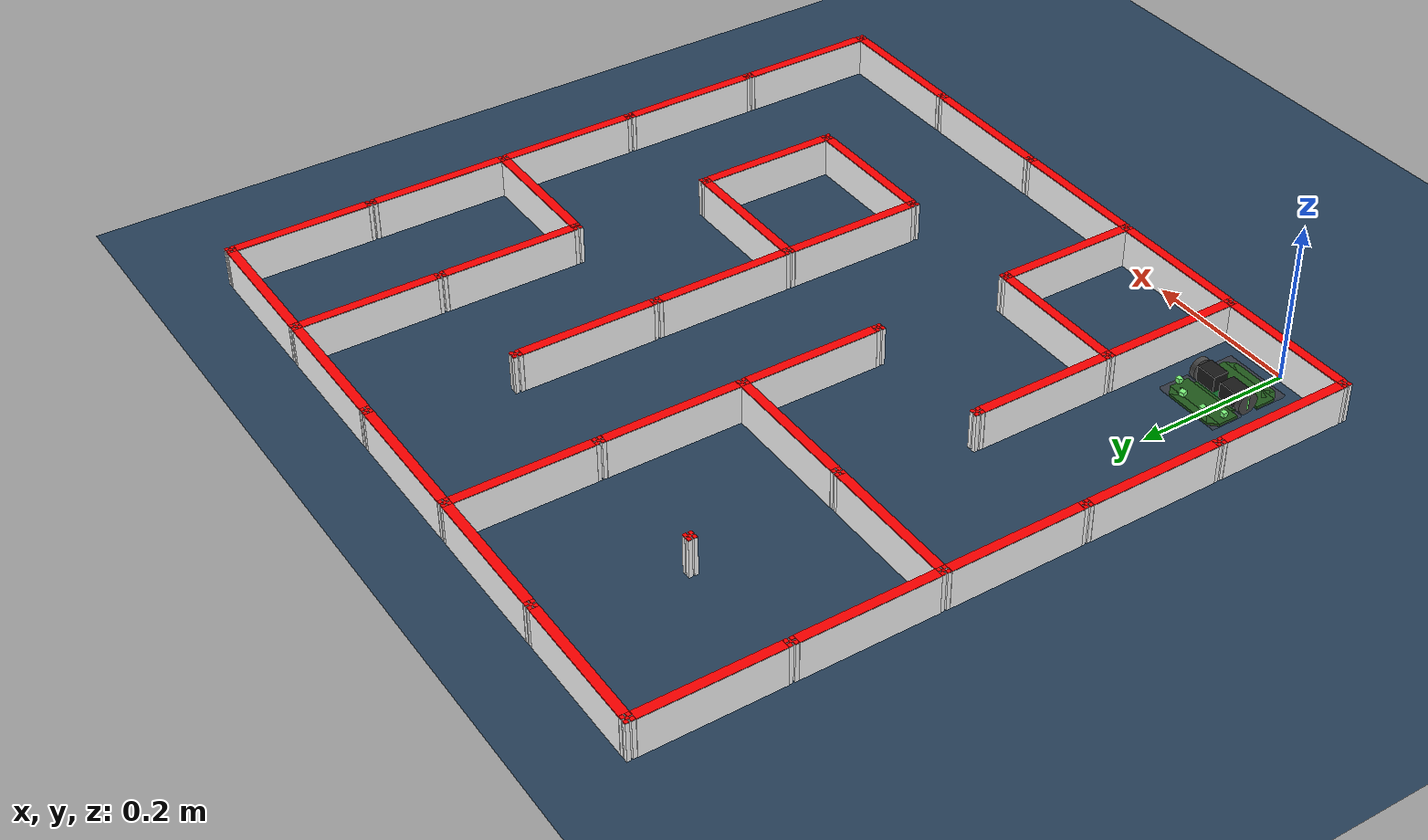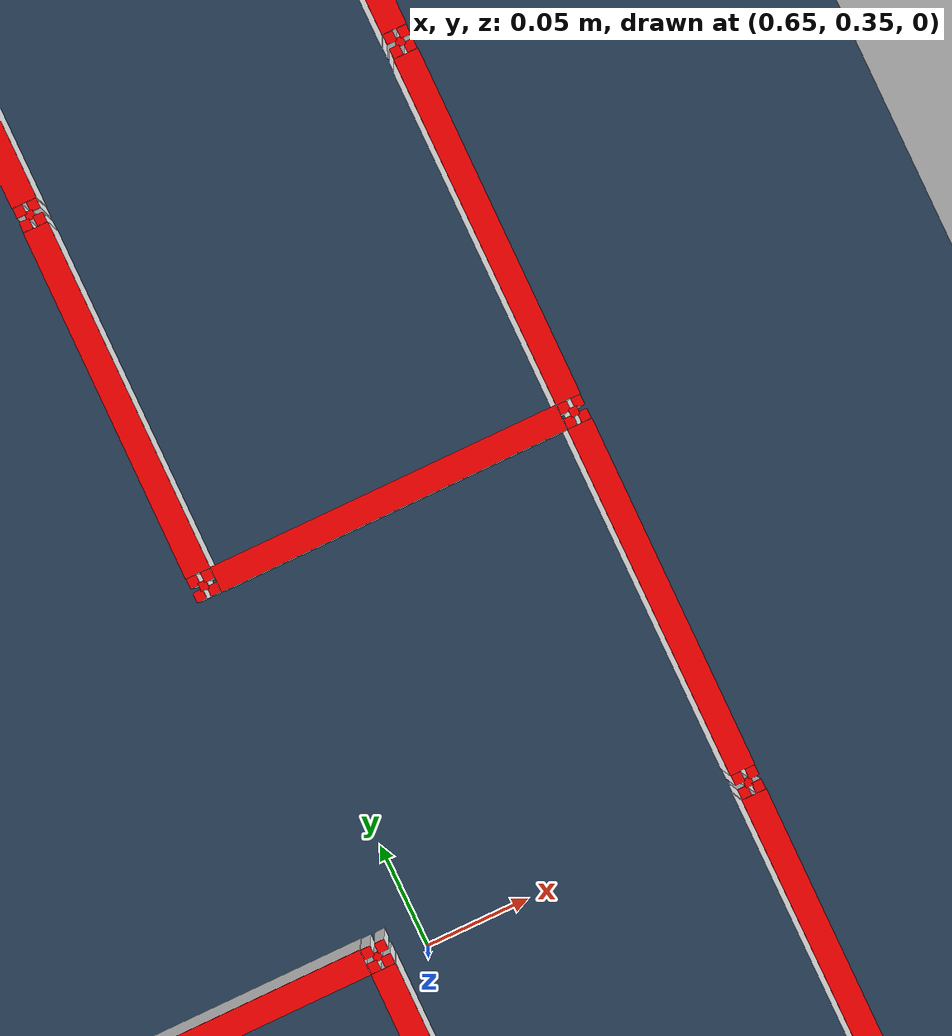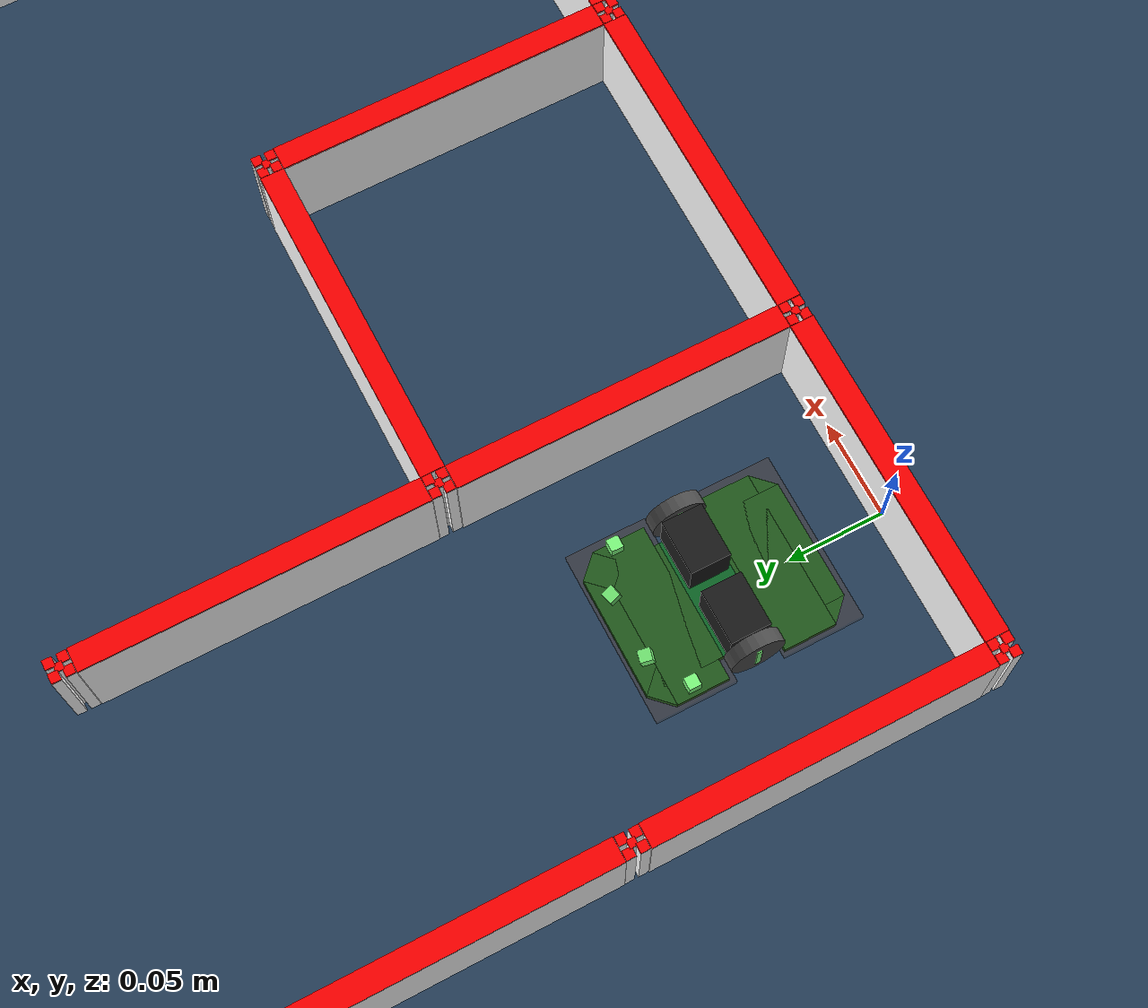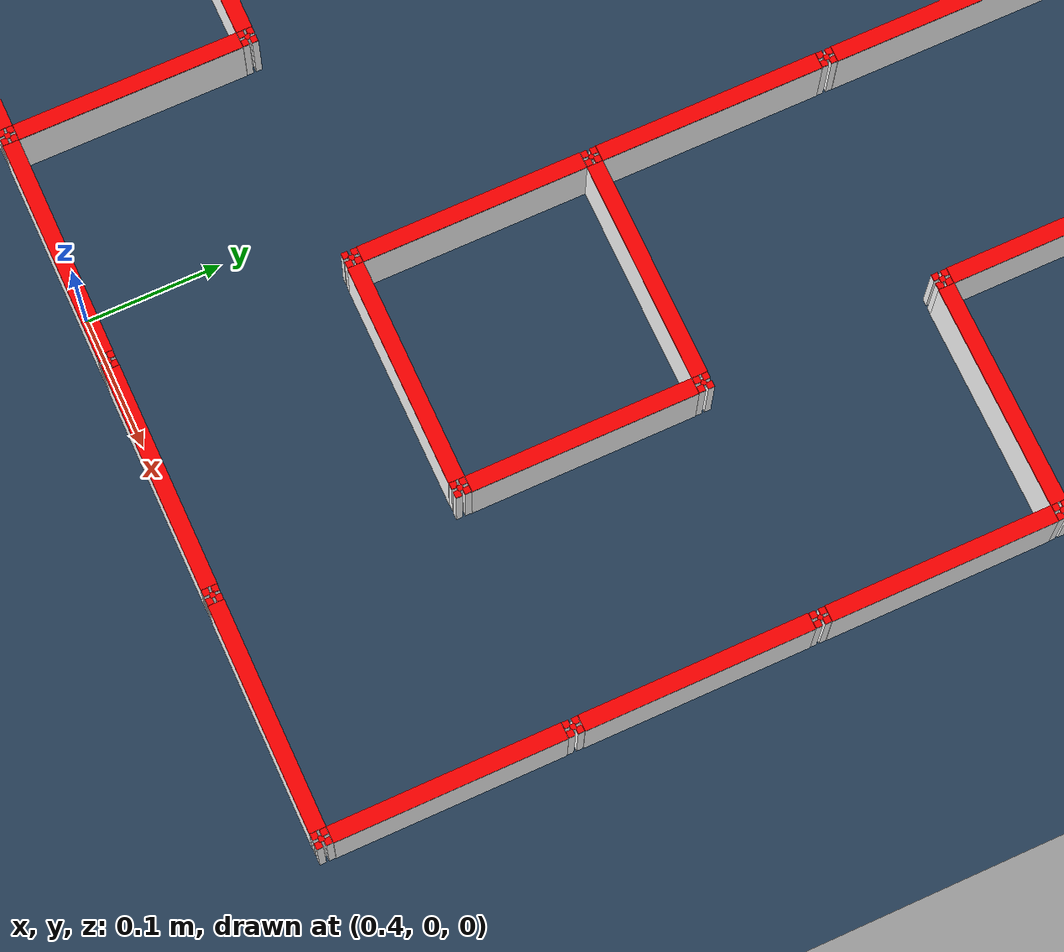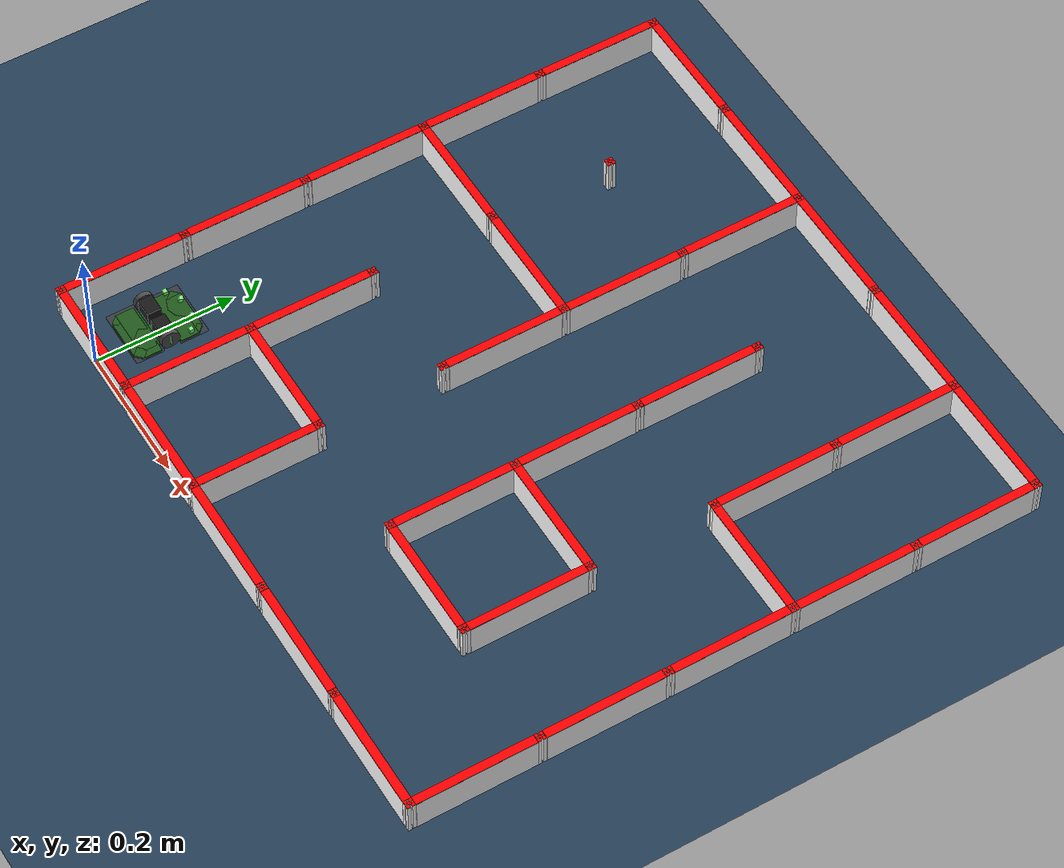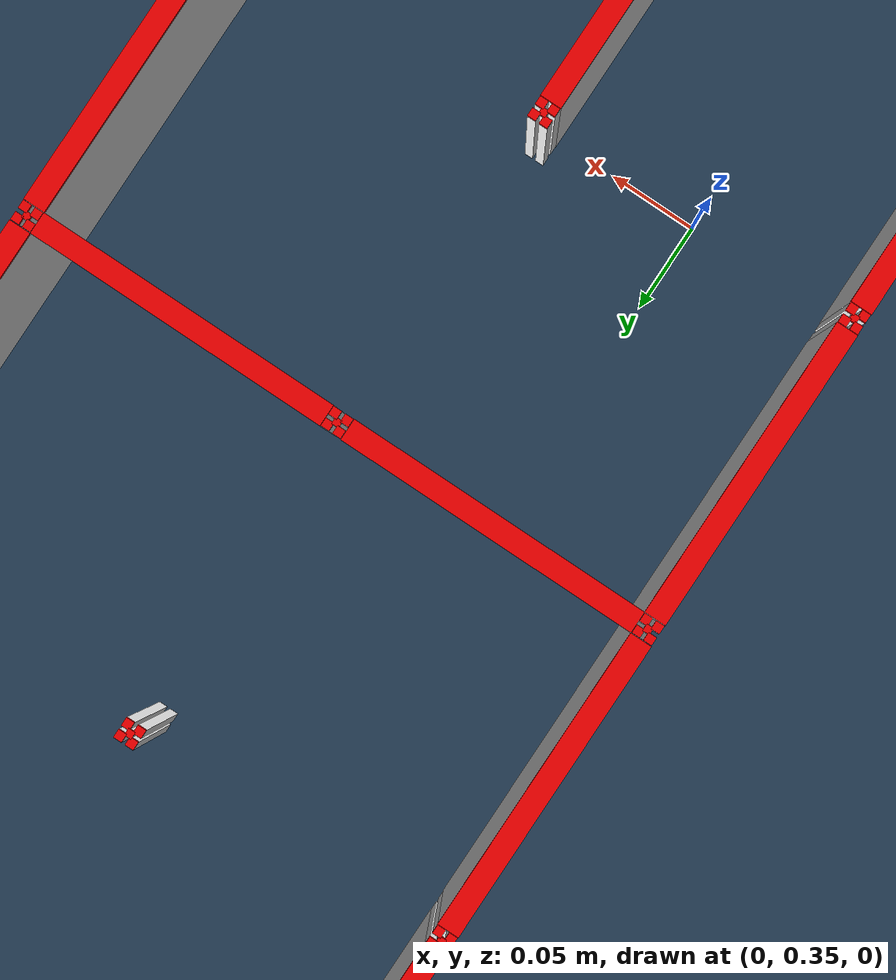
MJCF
<mujoco>
<compiler angle="degree" coordinate="local" inertiafromgeom="true" />
    <option integrator="RK4" timestep="0.001" />
    <asset>
        <texture type="skybox" builtin="gradient" rgb1="0.3 0.5 0.7" rgb2="0 0 0" width="512" height="3072"/>
        <texture type="2d" name="groundplane" builtin="checker" mark="edge" rgb1="0.2 0.3 0.4" rgb2="0.1 0.2 0.3" markrgb="0.8 0.8 0.8" width="300" height="300"/>
        <material name="groundplane" texture="groundplane" texuniform="true" texrepeat="5 5" reflectance="0.2"/>
    </asset>

    <worldbody>
        <light diffuse=".5 .5 .5" pos="0 0 10" dir="0 0 -1"/>
        <geom type="plane" size="1 1 .01" material="groundplane"/>

        <body pos="0.0 0.09 0.015" euler="0 0 90">
            <freejoint />
            <body name="torso" >
            <geom name="mein_body1" type="box" size="0.05 0.03 0.0016" friction="0.0 0.0 0.0" rgba="0.05 0.4 0.15 1" pos="0 0 0.001" mass="4.65e-3"/>
            <geom name="mein_body_chip1" type="box" size="0.00707 0.00707 0.0016" friction="0.0 0.0 0.0" rgba="0.05 0.4 0.15 1" pos="0.04 0.03 0.001" euler="0 0 45" mass="4.65e-3"/>
            <geom name="mein_body_chip2" type="box" size="0.00707 0.00707 0.0016" friction="0.0 0.0 0.0" rgba="0.05 0.4 0.15 1" pos="0.04 -0.03 0.001" euler="0 0 45" mass="4.65e-3"/>
            <geom name="mein_body_chip3" type="box" size="0.00707 0.00707 0.0016" friction="0.0 0.0 0.0" rgba="0.05 0.4 0.15 1" pos="-0.04 0.03 0.001" euler="0 0 45" mass="4.65e-3"/>
            <geom name="mein_body_chip4" type="box" size="0.00707 0.00707 0.0016" friction="0.0 0.0 0.0" rgba="0.05 0.4 0.15 1" pos="-0.04 -0.03 0.001" euler="0 0 45" mass="4.65e-3"/>
            <geom name="mein_body4" type="box" size="0.013 0.04 0.0016" friction="0.0 0.0 0.0" rgba="0.05 0.4 0.15 1" pos="-0.027 0 0.001" mass="4.65e-3"/>
            <geom name="mein_body5" type="box" size="0.013 0.04 0.0016" friction="0.0 0.0 0.0" rgba="0.05 0.4 0.15 1" pos="0.027 0 0.001" mass="4.65e-3"/>
                <site name = "hit_box" type = "box" size = "0.02 0.043 0.0016" pos="0.032 0 0.003" rgba=".5 .2 0 .1"/> 接触判定領域（この中に入ってるgeomが接触すると，センサ値としてその値を取得できる）
                <site name = "hit_box2" type = "box" size = "0.02 0.043 0.0016" pos="-0.032 0 0.003" rgba=".5 .2 0 .1"/>
                <camera name="camera_name" mode="track" pos="-0.2 0 1" euler="0 -20 -90" fovy="60"/> トラッキングカメラを装着
            </body>

            <site name="sensor_left_front" type="box" size="0.003 0.003 0.003" pos="0.031 0.036 0.01" zaxis="1 0 0.01" rgba=".5 1 .5 1"/>
              <!-- zaxisの３つめ　0.1でちょい上向き -->
            <site name="sensor_left_side" type="box" size="0.003 0.003 0.003" pos="0.043 0.016 0.01" zaxis="0.25 1 0" rgba=".5 1 .5 1"/>
            <site name="sensor_right_side" type="box" size="0.003 0.003 0.003" pos="0.043 -0.016 0.01" zaxis="0.25 -1 0" rgba=".5 1 .5 1"/>
            <site name="sensor_right_front" type="box" size="0.003 0.003 0.003" pos="0.031 -0.036 0.01" zaxis="1 0 0.01" rgba=".5 1 .5 1"/>

             <body name="left wheel" pos="-0.0 0.036 0.0125" zaxis="0 1 0">
                <joint name="left wheel joint" type="hinge" axis="0 0 1" limited="false" damping='5.4e-5' />

                <geom type="cylinder" size="0.0135 0.0035" rgba=".3 .3 0.3 1" mass="1.0e-2"/>
                <site type="box" size = "0.0012 0.008 0.004" rgba=".5 1 .5 1"/>
            </body>

            <body name="right wheel" pos="-0.0 -0.036 0.0125" zaxis="0 1 0">
                <joint name="right wheel joint" type="hinge" axis="0 0 1" limited="false" damping='5.4e-5' />
                <geom type="cylinder" size="0.0135 0.0035" rgba=".3 .3 0.3 1" mass="1.0e-2"/>
                <site type="box" size = "0.0012 0.008 0.004" rgba=".5 1 .5 1"/>
            </body>

            <body name="motorbox1" pos="0 -0.018 0.0135" >
                <geom type="box" size="0.01 0.0135 0.01" rgba="0.1 0.1 0.1 1" mass="5.52e-2"/>
            </body>

            <body name="motorbox2" pos="0 0.018 0.0135">
                <geom type="box" size="0.01 0.0135 0.01" rgba="0.1 0.1 0.1 1" mass="5.52e-2"/>
            </body>

        </body>
        <!--ベース板-->
        <body name="base_plate" pos="0.72 0.81 0.006">
            <geom type="plane" mass="0.1" size="0.861 0.861 0.006" rgba="0.2 0.2 0.2 1" friction="0.0 0.0 0.0"/>
        </body>
        <body name="wall1" pos="0 0 0.025"  euler="0 0 0">
            <body pos="0 0 -0.0005">
                <geom type="box" mass="0.1" size="0.084 0.006 0.0245" rgba="1 1 1 1"/>
            </body>
            <body pos="0 0 0.0245">
                <geom type="box" mass="0.001" size="0.084 0.006 0.0005" rgba="1 0 0 1"/>
            </body>
        </body>
        <body name="wall2" pos="0.18 0 0.025" euler="0 0 0">
            <body pos="0 0 -0.0005">
                <geom type="box" mass="0.1" size="0.084 0.006 0.0245" rgba="1 1 1 1"/>
            </body>
            <body pos="0 0 0.0245">
                <geom type="box" mass="0.001" size="0.084 0.006 0.0005" rgba="1 0 0 1"/>
            </body>
        </body>
        <body name="wall3" pos="0.36 0 0.025" euler="0 0 0">
            <body pos="0 0 -0.0005">
                <geom type="box" mass="0.1" size="0.084 0.006 0.0245" rgba="1 1 1 1"/>
            </body>
            <body pos="0 0 0.0245">
                <geom type="box" mass="0.001" size="0.084 0.006 0.0005" rgba="1 0 0 1"/>
            </body>
        </body>
        <body name="wall2dcccvfgrrrfff" pos="0.54 0 0.025" euler="0 0 0">
            <body pos="0 0 -0.0005">
                <geom type="box" mass="0.1" size="0.084 0.006 0.0245" rgba="1 1 1 1"/>
            </body>
            <body pos="0 0 0.0245">
                <geom type="box" mass="0.001" size="0.084 0.006 0.0005" rgba="1 0 0 1"/>
            </body>
        </body>
        <body name="wall3aaasswrtqqqqqq" pos="0.72 0 0.025" euler="0 0 0">
            <body pos="0 0 -0.0005">
                <geom type="box" mass="0.1" size="0.084 0.006 0.0245" rgba="1 1 1 1"/>
            </body>
            <body pos="0 0 0.0245">
                <geom type="box" mass="0.001" size="0.084 0.006 0.0005" rgba="1 0 0 1"/>
            </body>
        </body>

        <body name="wall4" pos="0.81 0.09 0.025"  euler="0 0 90">
            <body pos="0 0 -0.0005">
                <geom type="box" mass="0.1" size="0.084 0.006 0.0245" rgba="1 1 1 1"/>
            </body>
            <body pos="0 0 0.0245">
                <geom type="box" mass="0.001" size="0.084 0.006 0.0005" rgba="1 0 0 1"/>
            </body>
        </body>
        <body name="wall5" pos="0.81 0.27 0.025" euler="0 0 90">
            <body pos="0 0 -0.0005">
                <geom type="box" mass="0.1" size="0.084 0.006 0.0245" rgba="1 1 1 1"/>
            </body>
            <body pos="0 0 0.0245">
                <geom type="box" mass="0.001" size="0.084 0.006 0.0005" rgba="1 0 0 1"/>
            </body>
        </body>
        <body name="wall6" pos="0.81 0.45 0.025" euler="0 0 90">
            <body pos="0 0 -0.0005">
                <geom type="box" mass="0.1" size="0.084 0.006 0.0245" rgba="1 1 1 1"/>
            </body>
            <body pos="0 0 0.0245">
                <geom type="box" mass="0.001" size="0.084 0.006 0.0005" rgba="1 0 0 1"/>
            </body>
        </body>
        <body name="wall5feddddsss" pos="0.81 0.63 0.025" euler="0 0 90">
            <body pos="0 0 -0.0005">
                <geom type="box" mass="0.1" size="0.084 0.006 0.0245" rgba="1 1 1 1"/>
            </body>
            <body pos="0 0 0.0245">
                <geom type="box" mass="0.001" size="0.084 0.006 0.0005" rgba="1 0 0 1"/>
            </body>
        </body>
        <body name="wall6kuiioo" pos="0.81 0.81 0.025" euler="0 0 90">
            <body pos="0 0 -0.0005">
                <geom type="box" mass="0.1" size="0.084 0.006 0.0245" rgba="1 1 1 1"/>
            </body>
            <body pos="0 0 0.0245">
                <geom type="box" mass="0.001" size="0.084 0.006 0.0005" rgba="1 0 0 1"/>
            </body>
        </body>

        <body name="wall7" pos="-0.090 0.09 0.025"  euler="0 0 90">
            <body pos="0 0 -0.0005">
                <geom type="box" mass="0.1" size="0.084 0.006 0.0245" rgba="1 1 1 1"/>
            </body>
            <body pos="0 0 0.0245">
                <geom type="box" mass="0.001" size="0.084 0.006 0.0005" rgba="1 0 0 1"/>
            </body>
        </body>
        <body name="wall8" pos="-0.090 0.27 0.025" euler="0 0 90">
            <body pos="0 0 -0.0005">
                <geom type="box" mass="0.1" size="0.084 0.006 0.0245" rgba="1 1 1 1"/>
            </body>
            <body pos="0 0 0.0245">
                <geom type="box" mass="0.001" size="0.084 0.006 0.0005" rgba="1 0 0 1"/>
            </body>
        </body>
        <body name="wall9" pos="-0.090 0.45 0.025" euler="0 0 90">
            <body pos="0 0 -0.0005">
                <geom type="box" mass="0.1" size="0.084 0.006 0.0245" rgba="1 1 1 1"/>
            </body>
            <body pos="0 0 0.0245">
                <geom type="box" mass="0.001" size="0.084 0.006 0.0005" rgba="1 0 0 1"/>
            </body>
        </body>
        <body name="wall10" pos="-0.090 0.63 0.025" euler="0 0 90">
            <body pos="0 0 -0.0005">
                <geom type="box" mass="0.1" size="0.084 0.006 0.0245" rgba="1 1 1 1"/>
            </body>
            <body pos="0 0 0.0245">
                <geom type="box" mass="0.001" size="0.084 0.006 0.0005" rgba="1 0 0 1"/>
            </body>
        </body>
        <body name="wall11" pos="-0.090 0.81 0.025" euler="0 0 90">
            <body pos="0 0 -0.0005">
                <geom type="box" mass="0.1" size="0.084 0.006 0.0245" rgba="1 1 1 1"/>
            </body>
            <body pos="0 0 0.0245">
                <geom type="box" mass="0.001" size="0.084 0.006 0.0005" rgba="1 0 0 1"/>
            </body>
        </body>
        <body name="wala1" pos="0 0.9 0.025"  euler="0 0 0">
            <body pos="0 0 -0.0005">
                <geom type="box" mass="0.1" size="0.084 0.006 0.0245" rgba="1 1 1 1"/>
            </body>
            <body pos="0 0 0.0245">
                <geom type="box" mass="0.001" size="0.084 0.006 0.0005" rgba="1 0 0 1"/>
            </body>
        </body>
        <body name="waaaall2" pos="0.18 0.9 0.025" euler="0 0 0">
            <body pos="0 0 -0.0005">
                <geom type="box" mass="0.1" size="0.084 0.006 0.0245" rgba="1 1 1 1"/>
            </body>
            <body pos="0 0 0.0245">
                <geom type="box" mass="0.001" size="0.084 0.006 0.0005" rgba="1 0 0 1"/>
            </body>
        </body>
        <body name="waddll3" pos="0.36 0.9 0.025" euler="0 0 0">
            <body pos="0 0 -0.0005">
                <geom type="box" mass="0.1" size="0.084 0.006 0.0245" rgba="1 1 1 1"/>
            </body>
            <body pos="0 0 0.0245">
                <geom type="box" mass="0.001" size="0.084 0.006 0.0005" rgba="1 0 0 1"/>
            </body>
        </body>
        <body name="walccvfgrrrfff" pos="0.54 0.9 0.025" euler="0 0 0">
            <body pos="0 0 -0.0005">
                <geom type="box" mass="0.1" size="0.084 0.006 0.0245" rgba="1 1 1 1"/>
            </body>
            <body pos="0 0 0.0245">
                <geom type="box" mass="0.001" size="0.084 0.006 0.0005" rgba="1 0 0 1"/>
            </body>
        </body>
        <body name="wallqqq" pos="0.72 0.9 0.025" euler="0 0 0">
            <body pos="0 0 -0.0005">
                <geom type="box" mass="0.1" size="0.084 0.006 0.0245" rgba="1 1 1 1"/>
            </body>
            <body pos="0 0 0.0245">
                <geom type="box" mass="0.001" size="0.084 0.006 0.0005" rgba="1 0 0 1"/>
            </body>
        </body>

            <!--ここまで外の壁，ここから中の壁-->
        <body name="wall13" pos="0.09 0.09 0.025" euler="0 0 90">
            <body pos="0 0 -0.0005">
                <geom type="box" mass="0.1" size="0.084 0.006 0.0245" rgba="1 1 1 1"/>
            </body>
            <body pos="0 0 0.0245">
                <geom type="box" mass="0.001" size="0.084 0.006 0.0005" rgba="1 0 0 1"/>
            </body>
        </body>
        <body name="wallsdss13" pos="0.09 0.27 0.025" euler="0 0 90">
            <body pos="0 0 -0.0005">
                <geom type="box" mass="0.1" size="0.084 0.006 0.0245" rgba="1 1 1 1"/>
            </body>
            <body pos="0 0 0.0245">
                <geom type="box" mass="0.001" size="0.084 0.006 0.0005" rgba="1 0 0 1"/>
            </body>
        </body>

        <body name="wall14" pos="0.27 0.45 0.025" euler="0 0 90">
            <body pos="0 0 -0.0005">
                <geom type="box" mass="0.1" size="0.084 0.006 0.0245" rgba="1 1 1 1"/>
            </body>
            <body pos="0 0 0.0245">
                <geom type="box" mass="0.001" size="0.084 0.006 0.0005" rgba="1 0 0 1"/>
            </body>
        </body>

        <body name="wall15" pos="0.18 0.18 0.025" euler="0 0 0">
            <body pos="0 0 -0.0005">
                <geom type="box" mass="0.1" size="0.084 0.006 0.0245" rgba="1 1 1 1"/>
            </body>
            <body pos="0 0 0.0245">
                <geom type="box" mass="0.001" size="0.084 0.006 0.0005" rgba="1 0 0 1"/>
            </body>
        </body>

        <body name="wall16" pos="0.27 0.09 0.025" euler="0 0 90">
            <body pos="0 0 -0.0005">
                <geom type="box" mass="0.1" size="0.084 0.006 0.0245" rgba="1 1 1 1"/>
            </body>
            <body pos="0 0 0.0245">
                <geom type="box" mass="0.001" size="0.084 0.006 0.0005" rgba="1 0 0 1"/>
            </body>
        </body>
        <body name="wallaaaa13" pos="0.0 0.54 0.025" euler="0 0 0">
            <body pos="0 0 -0.0005">
                <geom type="box" mass="0.1" size="0.084 0.006 0.0245" rgba="1 1 1 1"/>
            </body>
            <body pos="0 0 0.0245">
                <geom type="box" mass="0.001" size="0.084 0.006 0.0005" rgba="1 0 0 1"/>
            </body>
        </body>
        <body name="wallaaasssxa13" pos="0.18 0.54 0.025" euler="0 0 0">
            <body pos="0 0 -0.0005">
                <geom type="box" mass="0.1" size="0.084 0.006 0.0245" rgba="1 1 1 1"/>
            </body>
            <body pos="0 0 0.0245">
                <geom type="box" mass="0.001" size="0.084 0.006 0.0005" rgba="1 0 0 1"/>
            </body>
        </body>
        <body name="allsssq16" pos="0.27 0.63 0.025" euler="0 0 90">
            <body pos="0 0 -0.0005">
                <geom type="box" mass="0.1" size="0.084 0.006 0.0245" rgba="1 1 1 1"/>
            </body>
            <body pos="0 0 0.0245">
                <geom type="box" mass="0.001" size="0.084 0.006 0.0005" rgba="1 0 0 1"/>
            </body>
            </body>

        <body name="wsspq16" pos="0.63 0.81 0.025" euler="0 0 90">
            <body pos="0 0 -0.0005">
                <geom type="box" mass="0.1" size="0.084 0.006 0.0245" rgba="1 1 1 1"/>
            </body>
            <body pos="0 0 0.0245">
                <geom type="box" mass="0.001" size="0.084 0.006 0.0005" rgba="1 0 0 1"/>
            </body>
            </body>
            <body name="allsszsq16" pos="0.27 0.81 0.025" euler="0 0 90">
            <body pos="0 0 -0.0005">
                <geom type="box" mass="0.1" size="0.084 0.006 0.0245" rgba="1 1 1 1"/>
            </body>
            <body pos="0 0 0.0245">
                <geom type="box" mass="0.001" size="0.084 0.006 0.0005" rgba="1 0 0 1"/>
            </body>
            </body>

        <body name="wsspyuq16" pos="0.72 0.54 0.025" euler="0 0 0">
            <body pos="0 0 -0.0005">
                <geom type="box" mass="0.1" size="0.084 0.006 0.0245" rgba="1 1 1 1"/>
            </body>
            <body pos="0 0 0.0245">
                <geom type="box" mass="0.001" size="0.084 0.006 0.0005" rgba="1 0 0 1"/>
            </body>
            </body>
            <body name="wsspyxxzsuq16" pos="0.63 0.63 0.025" euler="0 0 90">
            <body pos="0 0 -0.0005">
                <geom type="box" mass="0.1" size="0.084 0.006 0.0245" rgba="1 1 1 1"/>
            </body>
            <body pos="0 0 0.0245">
                <geom type="box" mass="0.001" size="0.084 0.006 0.0005" rgba="1 0 0 1"/>
            </body>
            </body>
        <body name="oiouq16" pos="0.45 0.63 0.025" euler="0 0 90">
            <body pos="0 0 -0.0005">
                <geom type="box" mass="0.1" size="0.084 0.006 0.0245" rgba="1 1 1 1"/>
            </body>
            <body pos="0 0 0.0245">
                <geom type="box" mass="0.001" size="0.084 0.006 0.0005" rgba="1 0 0 1"/>
            </body>
            </body>
        <body name="oizsouq16" pos="0.45 0.45 0.025" euler="0 0 90">
            <body pos="0 0 -0.0005">
                <geom type="box" mass="0.1" size="0.084 0.006 0.0245" rgba="1 1 1 1"/>
            </body>
            <body pos="0 0 0.0245">
                <geom type="box" mass="0.001" size="0.084 0.006 0.0005" rgba="1 0 0 1"/>
            </body>
            </body>
        <body name="oisdeq16" pos="0.45 0.27 0.025" euler="0 0 90">
            <body pos="0 0 -0.0005">
                <geom type="box" mass="0.1" size="0.084 0.006 0.0245" rgba="1 1 1 1"/>
            </body>
            <body pos="0 0 0.0245">
                <geom type="box" mass="0.001" size="0.084 0.006 0.0005" rgba="1 0 0 1"/>
            </body>
            </body>
        <body name="oaahq16" pos="0.63 0.27 0.025" euler="0 0 90">
            <body pos="0 0 -0.0005">
                <geom type="box" mass="0.1" size="0.084 0.006 0.0245" rgba="1 1 1 1"/>
            </body>
            <body pos="0 0 0.0245">
                <geom type="box" mass="0.001" size="0.084 0.006 0.0005" rgba="1 0 0 1"/>
            </body>
            </body>
        <body name="wsstytq16" pos="0.54 0.18 0.025" euler="0 0 0">
            <body pos="0 0 -0.0005">
                <geom type="box" mass="0.1" size="0.084 0.006 0.0245" rgba="1 1 1 1"/>
            </body>
            <body pos="0 0 0.0245">
                <geom type="box" mass="0.001" size="0.084 0.006 0.0005" rgba="1 0 0 1"/>
            </body>
            </body>
        <body name="wsdfretq16" pos="0.54 0.36 0.025" euler="0 0 0">
            <body pos="0 0 -0.0005">
                <geom type="box" mass="0.1" size="0.084 0.006 0.0245" rgba="1 1 1 1"/>
            </body>
            <body pos="0 0 0.0245">
                <geom type="box" mass="0.001" size="0.084 0.006 0.0005" rgba="1 0 0 1"/>
            </body>
            </body>

        <body pos="-0.09 0 0.025">
            <body pos="0.003375 0.003375 -0.0005">
                <geom type="box" mass="0.01" size="0.002375 0.002375 0.0245" rgba="1 1 1 1"/>
            </body>
            <body pos="0.003375 -0.003375 -0.0005">
                <geom type="box" mass="0.01" size="0.002375 0.002375 0.0245" rgba="1 1 1 1"/>
            </body>
            <body pos="-0.003375 0.003375 -0.0005">
                <geom type="box" mass="0.01" size="0.002375 0.002375 0.0245" rgba="1 1 1 1"/>
            </body>
            <body pos="-0.003375 -0.003375 -0.0005">
                <geom type="box" mass="0.01" size="0.002375 0.002375 0.0245" rgba="1 1 1 1"/>
            </body>
            <body pos="0 0 -0.0005">
                <geom type="box" mass="0.01" size="0.002 0.002 0.0245" rgba="1 1 1 1"/>
            </body>
            <!--柱上赤蓋-->
            <body pos="0.003375 0.003375 0.0245">
                <geom type="box" mass="0.01" size="0.002375 0.002375 0.0005" rgba="1 0 0 1"/>
            </body>
            <body pos="0.003375 -0.003375 0.0245">
                <geom type="box" mass="0.01" size="0.002375 0.002375 0.0005" rgba="1 0 0 1"/>
            </body>
            <body pos="-0.003375 0.003375 0.0245">
                <geom type="box" mass="0.01" size="0.002375 0.002375 0.0005" rgba="1 0 0 1"/>
            </body>
            <body pos="-0.003375 -0.003375 0.0245">
                <geom type="box" mass="0.01" size="0.002375 0.002375 0.0005" rgba="1 0 0 1"/>
            </body>
            <body pos="0 0 0.0245">
                <geom type="box" mass="0.01" size="0.002 0.002 0.0005" rgba="1 0 0 1"/>
            </body>
        </body>
        <body pos="0.09 0 0.025">
            <body pos="0.003375 0.003375 -0.0005">
                <geom type="box" mass="0.01" size="0.002375 0.002375 0.0245" rgba="1 1 1 1"/>
            </body>
            <body pos="0.003375 -0.003375 -0.0005">
                <geom type="box" mass="0.01" size="0.002375 0.002375 0.0245" rgba="1 1 1 1"/>
            </body>
            <body pos="-0.003375 0.003375 -0.0005">
                <geom type="box" mass="0.01" size="0.002375 0.002375 0.0245" rgba="1 1 1 1"/>
            </body>
            <body pos="-0.003375 -0.003375 -0.0005">
                <geom type="box" mass="0.01" size="0.002375 0.002375 0.0245" rgba="1 1 1 1"/>
            </body>
            <body pos="0 0 -0.0005">
                <geom type="box" mass="0.01" size="0.002 0.002 0.0245" rgba="1 1 1 1"/>
            </body>
            <!--柱上赤蓋-->
            <body pos="0.003375 0.003375 0.0245">
                <geom type="box" mass="0.01" size="0.002375 0.002375 0.0005" rgba="1 0 0 1"/>
            </body>
            <body pos="0.003375 -0.003375 0.0245">
                <geom type="box" mass="0.01" size="0.002375 0.002375 0.0005" rgba="1 0 0 1"/>
            </body>
            <body pos="-0.003375 0.003375 0.0245">
                <geom type="box" mass="0.01" size="0.002375 0.002375 0.0005" rgba="1 0 0 1"/>
            </body>
            <body pos="-0.003375 -0.003375 0.0245">
                <geom type="box" mass="0.01" size="0.002375 0.002375 0.0005" rgba="1 0 0 1"/>
            </body>
            <body pos="0 0 0.0245">
                <geom type="box" mass="0.01" size="0.002 0.002 0.0005" rgba="1 0 0 1"/>
            </body>
        </body>
        <body pos="0.27 0 0.025">
            <body pos="0.003375 0.003375 -0.0005">
                <geom type="box" mass="0.01" size="0.002375 0.002375 0.0245" rgba="1 1 1 1"/>
            </body>
            <body pos="0.003375 -0.003375 -0.0005">
                <geom type="box" mass="0.01" size="0.002375 0.002375 0.0245" rgba="1 1 1 1"/>
            </body>
            <body pos="-0.003375 0.003375 -0.0005">
                <geom type="box" mass="0.01" size="0.002375 0.002375 0.0245" rgba="1 1 1 1"/>
            </body>
            <body pos="-0.003375 -0.003375 -0.0005">
                <geom type="box" mass="0.01" size="0.002375 0.002375 0.0245" rgba="1 1 1 1"/>
            </body>
            <body pos="0 0 -0.0005">
                <geom type="box" mass="0.01" size="0.002 0.002 0.0245" rgba="1 1 1 1"/>
            </body>
            <!--柱上赤蓋-->
            <body pos="0.003375 0.003375 0.0245">
                <geom type="box" mass="0.01" size="0.002375 0.002375 0.0005" rgba="1 0 0 1"/>
            </body>
            <body pos="0.003375 -0.003375 0.0245">
                <geom type="box" mass="0.01" size="0.002375 0.002375 0.0005" rgba="1 0 0 1"/>
            </body>
            <body pos="-0.003375 0.003375 0.0245">
                <geom type="box" mass="0.01" size="0.002375 0.002375 0.0005" rgba="1 0 0 1"/>
            </body>
            <body pos="-0.003375 -0.003375 0.0245">
                <geom type="box" mass="0.01" size="0.002375 0.002375 0.0005" rgba="1 0 0 1"/>
            </body>
            <body pos="0 0 0.0245">
                <geom type="box" mass="0.01" size="0.002 0.002 0.0005" rgba="1 0 0 1"/>
            </body>
        </body>
        <body pos="0.45 0 0.025">
            <body pos="0.003375 0.003375 -0.0005">
                <geom type="box" mass="0.01" size="0.002375 0.002375 0.0245" rgba="1 1 1 1"/>
            </body>
            <body pos="0.003375 -0.003375 -0.0005">
                <geom type="box" mass="0.01" size="0.002375 0.002375 0.0245" rgba="1 1 1 1"/>
            </body>
            <body pos="-0.003375 0.003375 -0.0005">
                <geom type="box" mass="0.01" size="0.002375 0.002375 0.0245" rgba="1 1 1 1"/>
            </body>
            <body pos="-0.003375 -0.003375 -0.0005">
                <geom type="box" mass="0.01" size="0.002375 0.002375 0.0245" rgba="1 1 1 1"/>
            </body>
            <body pos="0 0 -0.0005">
                <geom type="box" mass="0.01" size="0.002 0.002 0.0245" rgba="1 1 1 1"/>
            </body>
            <!--柱上赤蓋-->
            <body pos="0.003375 0.003375 0.0245">
                <geom type="box" mass="0.01" size="0.002375 0.002375 0.0005" rgba="1 0 0 1"/>
            </body>
            <body pos="0.003375 -0.003375 0.0245">
                <geom type="box" mass="0.01" size="0.002375 0.002375 0.0005" rgba="1 0 0 1"/>
            </body>
            <body pos="-0.003375 0.003375 0.0245">
                <geom type="box" mass="0.01" size="0.002375 0.002375 0.0005" rgba="1 0 0 1"/>
            </body>
            <body pos="-0.003375 -0.003375 0.0245">
                <geom type="box" mass="0.01" size="0.002375 0.002375 0.0005" rgba="1 0 0 1"/>
            </body>
            <body pos="0 0 0.0245">
                <geom type="box" mass="0.01" size="0.002 0.002 0.0005" rgba="1 0 0 1"/>
            </body>
        </body>
        <body pos="0.63 0 0.025">
            <body pos="0.003375 0.003375 -0.0005">
                <geom type="box" mass="0.01" size="0.002375 0.002375 0.0245" rgba="1 1 1 1"/>
            </body>
            <body pos="0.003375 -0.003375 -0.0005">
                <geom type="box" mass="0.01" size="0.002375 0.002375 0.0245" rgba="1 1 1 1"/>
            </body>
            <body pos="-0.003375 0.003375 -0.0005">
                <geom type="box" mass="0.01" size="0.002375 0.002375 0.0245" rgba="1 1 1 1"/>
            </body>
            <body pos="-0.003375 -0.003375 -0.0005">
                <geom type="box" mass="0.01" size="0.002375 0.002375 0.0245" rgba="1 1 1 1"/>
            </body>
            <body pos="0 0 -0.0005">
                <geom type="box" mass="0.01" size="0.002 0.002 0.0245" rgba="1 1 1 1"/>
            </body>
            <!--柱上赤蓋-->
            <body pos="0.003375 0.003375 0.0245">
                <geom type="box" mass="0.01" size="0.002375 0.002375 0.0005" rgba="1 0 0 1"/>
            </body>
            <body pos="0.003375 -0.003375 0.0245">
                <geom type="box" mass="0.01" size="0.002375 0.002375 0.0005" rgba="1 0 0 1"/>
            </body>
            <body pos="-0.003375 0.003375 0.0245">
                <geom type="box" mass="0.01" size="0.002375 0.002375 0.0005" rgba="1 0 0 1"/>
            </body>
            <body pos="-0.003375 -0.003375 0.0245">
                <geom type="box" mass="0.01" size="0.002375 0.002375 0.0005" rgba="1 0 0 1"/>
            </body>
            <body pos="0 0 0.0245">
                <geom type="box" mass="0.01" size="0.002 0.002 0.0005" rgba="1 0 0 1"/>
            </body>
        </body>
        <body pos="0.81 0 0.025">
            <body pos="0.003375 0.003375 -0.0005">
                <geom type="box" mass="0.01" size="0.002375 0.002375 0.0245" rgba="1 1 1 1"/>
            </body>
            <body pos="0.003375 -0.003375 -0.0005">
                <geom type="box" mass="0.01" size="0.002375 0.002375 0.0245" rgba="1 1 1 1"/>
            </body>
            <body pos="-0.003375 0.003375 -0.0005">
                <geom type="box" mass="0.01" size="0.002375 0.002375 0.0245" rgba="1 1 1 1"/>
            </body>
            <body pos="-0.003375 -0.003375 -0.0005">
                <geom type="box" mass="0.01" size="0.002375 0.002375 0.0245" rgba="1 1 1 1"/>
            </body>
            <body pos="0 0 -0.0005">
                <geom type="box" mass="0.01" size="0.002 0.002 0.0245" rgba="1 1 1 1"/>
            </body>
            <!--柱上赤蓋-->
            <body pos="0.003375 0.003375 0.0245">
                <geom type="box" mass="0.01" size="0.002375 0.002375 0.0005" rgba="1 0 0 1"/>
            </body>
            <body pos="0.003375 -0.003375 0.0245">
                <geom type="box" mass="0.01" size="0.002375 0.002375 0.0005" rgba="1 0 0 1"/>
            </body>
            <body pos="-0.003375 0.003375 0.0245">
                <geom type="box" mass="0.01" size="0.002375 0.002375 0.0005" rgba="1 0 0 1"/>
            </body>
            <body pos="-0.003375 -0.003375 0.0245">
                <geom type="box" mass="0.01" size="0.002375 0.002375 0.0005" rgba="1 0 0 1"/>
            </body>
            <body pos="0 0 0.0245">
                <geom type="box" mass="0.01" size="0.002 0.002 0.0005" rgba="1 0 0 1"/>
            </body>
        </body>
##########################################################################################################################################################
###################################################################田植え一辺終わりました#######################################################################
##########################################################################################################################################################
        <body pos="0.63 0.18 0.025">
            <body pos="0.003375 0.003375 -0.0005">
                <geom type="box" mass="0.01" size="0.002375 0.002375 0.0245" rgba="1 1 1 1"/>
            </body>
            <body pos="0.003375 -0.003375 -0.0005">
                <geom type="box" mass="0.01" size="0.002375 0.002375 0.0245" rgba="1 1 1 1"/>
            </body>
            <body pos="-0.003375 0.003375 -0.0005">
                <geom type="box" mass="0.01" size="0.002375 0.002375 0.0245" rgba="1 1 1 1"/>
            </body>
            <body pos="-0.003375 -0.003375 -0.0005">
                <geom type="box" mass="0.01" size="0.002375 0.002375 0.0245" rgba="1 1 1 1"/>
            </body>
            <body pos="0 0 -0.0005">
                <geom type="box" mass="0.01" size="0.002 0.002 0.0245" rgba="1 1 1 1"/>
            </body>
            <!--柱上赤蓋-->
            <body pos="0.003375 0.003375 0.0245">
                <geom type="box" mass="0.01" size="0.002375 0.002375 0.0005" rgba="1 0 0 1"/>
            </body>
            <body pos="0.003375 -0.003375 0.0245">
                <geom type="box" mass="0.01" size="0.002375 0.002375 0.0005" rgba="1 0 0 1"/>
            </body>
            <body pos="-0.003375 0.003375 0.0245">
                <geom type="box" mass="0.01" size="0.002375 0.002375 0.0005" rgba="1 0 0 1"/>
            </body>
            <body pos="-0.003375 -0.003375 0.0245">
                <geom type="box" mass="0.01" size="0.002375 0.002375 0.0005" rgba="1 0 0 1"/>
            </body>
            <body pos="0 0 0.0245">
                <geom type="box" mass="0.01" size="0.002 0.002 0.0005" rgba="1 0 0 1"/>
            </body>
        </body>
        <body pos="0.81 0.18 0.025">
            <body pos="0.003375 0.003375 -0.0005">
                <geom type="box" mass="0.01" size="0.002375 0.002375 0.0245" rgba="1 1 1 1"/>
            </body>
            <body pos="0.003375 -0.003375 -0.0005">
                <geom type="box" mass="0.01" size="0.002375 0.002375 0.0245" rgba="1 1 1 1"/>
            </body>
            <body pos="-0.003375 0.003375 -0.0005">
                <geom type="box" mass="0.01" size="0.002375 0.002375 0.0245" rgba="1 1 1 1"/>
            </body>
            <body pos="-0.003375 -0.003375 -0.0005">
                <geom type="box" mass="0.01" size="0.002375 0.002375 0.0245" rgba="1 1 1 1"/>
            </body>
            <body pos="0 0 -0.0005">
                <geom type="box" mass="0.01" size="0.002 0.002 0.0245" rgba="1 1 1 1"/>
            </body>
            <!--柱上赤蓋-->
            <body pos="0.003375 0.003375 0.0245">
                <geom type="box" mass="0.01" size="0.002375 0.002375 0.0005" rgba="1 0 0 1"/>
            </body>
            <body pos="0.003375 -0.003375 0.0245">
                <geom type="box" mass="0.01" size="0.002375 0.002375 0.0005" rgba="1 0 0 1"/>
            </body>
            <body pos="-0.003375 0.003375 0.0245">
                <geom type="box" mass="0.01" size="0.002375 0.002375 0.0005" rgba="1 0 0 1"/>
            </body>
            <body pos="-0.003375 -0.003375 0.0245">
                <geom type="box" mass="0.01" size="0.002375 0.002375 0.0005" rgba="1 0 0 1"/>
            </body>
            <body pos="0 0 0.0245">
                <geom type="box" mass="0.01" size="0.002 0.002 0.0005" rgba="1 0 0 1"/>
            </body>
        </body>
        ##########################################################################################################################################################
###################################################################田植え２辺終わりました#######################################################################
##########################################################################################################################################################
        <body pos="0.63 0.36 0.025">
            <body pos="0.003375 0.003375 -0.0005">
                <geom type="box" mass="0.01" size="0.002375 0.002375 0.0245" rgba="1 1 1 1"/>
            </body>
            <body pos="0.003375 -0.003375 -0.0005">
                <geom type="box" mass="0.01" size="0.002375 0.002375 0.0245" rgba="1 1 1 1"/>
            </body>
            <body pos="-0.003375 0.003375 -0.0005">
                <geom type="box" mass="0.01" size="0.002375 0.002375 0.0245" rgba="1 1 1 1"/>
            </body>
            <body pos="-0.003375 -0.003375 -0.0005">
                <geom type="box" mass="0.01" size="0.002375 0.002375 0.0245" rgba="1 1 1 1"/>
            </body>
            <body pos="0 0 -0.0005">
                <geom type="box" mass="0.01" size="0.002 0.002 0.0245" rgba="1 1 1 1"/>
            </body>
            <!--柱上赤蓋-->
            <body pos="0.003375 0.003375 0.0245">
                <geom type="box" mass="0.01" size="0.002375 0.002375 0.0005" rgba="1 0 0 1"/>
            </body>
            <body pos="0.003375 -0.003375 0.0245">
                <geom type="box" mass="0.01" size="0.002375 0.002375 0.0005" rgba="1 0 0 1"/>
            </body>
            <body pos="-0.003375 0.003375 0.0245">
                <geom type="box" mass="0.01" size="0.002375 0.002375 0.0005" rgba="1 0 0 1"/>
            </body>
            <body pos="-0.003375 -0.003375 0.0245">
                <geom type="box" mass="0.01" size="0.002375 0.002375 0.0005" rgba="1 0 0 1"/>
            </body>
            <body pos="0 0 0.0245">
                <geom type="box" mass="0.01" size="0.002 0.002 0.0005" rgba="1 0 0 1"/>
            </body>
        </body>
        <body pos="0.81 0.36 0.025">
            <body pos="0.003375 0.003375 -0.0005">
                <geom type="box" mass="0.01" size="0.002375 0.002375 0.0245" rgba="1 1 1 1"/>
            </body>
            <body pos="0.003375 -0.003375 -0.0005">
                <geom type="box" mass="0.01" size="0.002375 0.002375 0.0245" rgba="1 1 1 1"/>
            </body>
            <body pos="-0.003375 0.003375 -0.0005">
                <geom type="box" mass="0.01" size="0.002375 0.002375 0.0245" rgba="1 1 1 1"/>
            </body>
            <body pos="-0.003375 -0.003375 -0.0005">
                <geom type="box" mass="0.01" size="0.002375 0.002375 0.0245" rgba="1 1 1 1"/>
            </body>
            <body pos="0 0 -0.0005">
                <geom type="box" mass="0.01" size="0.002 0.002 0.0245" rgba="1 1 1 1"/>
            </body>
            <!--柱上赤蓋-->
            <body pos="0.003375 0.003375 0.0245">
                <geom type="box" mass="0.01" size="0.002375 0.002375 0.0005" rgba="1 0 0 1"/>
            </body>
            <body pos="0.003375 -0.003375 0.0245">
                <geom type="box" mass="0.01" size="0.002375 0.002375 0.0005" rgba="1 0 0 1"/>
            </body>
            <body pos="-0.003375 0.003375 0.0245">
                <geom type="box" mass="0.01" size="0.002375 0.002375 0.0005" rgba="1 0 0 1"/>
            </body>
            <body pos="-0.003375 -0.003375 0.0245">
                <geom type="box" mass="0.01" size="0.002375 0.002375 0.0005" rgba="1 0 0 1"/>
            </body>
            <body pos="0 0 0.0245">
                <geom type="box" mass="0.01" size="0.002 0.002 0.0005" rgba="1 0 0 1"/>
            </body>
        </body>
        ##########################################################################################################################################################
###################################################################田植え3辺終わりました#######################################################################
##########################################################################################################################################################
        <body pos="0.63 0.54 0.025">
            <body pos="0.003375 0.003375 -0.0005">
                <geom type="box" mass="0.01" size="0.002375 0.002375 0.0245" rgba="1 1 1 1"/>
            </body>
            <body pos="0.003375 -0.003375 -0.0005">
                <geom type="box" mass="0.01" size="0.002375 0.002375 0.0245" rgba="1 1 1 1"/>
            </body>
            <body pos="-0.003375 0.003375 -0.0005">
                <geom type="box" mass="0.01" size="0.002375 0.002375 0.0245" rgba="1 1 1 1"/>
            </body>
            <body pos="-0.003375 -0.003375 -0.0005">
                <geom type="box" mass="0.01" size="0.002375 0.002375 0.0245" rgba="1 1 1 1"/>
            </body>
            <body pos="0 0 -0.0005">
                <geom type="box" mass="0.01" size="0.002 0.002 0.0245" rgba="1 1 1 1"/>
            </body>
            <!--柱上赤蓋-->
            <body pos="0.003375 0.003375 0.0245">
                <geom type="box" mass="0.01" size="0.002375 0.002375 0.0005" rgba="1 0 0 1"/>
            </body>
            <body pos="0.003375 -0.003375 0.0245">
                <geom type="box" mass="0.01" size="0.002375 0.002375 0.0005" rgba="1 0 0 1"/>
            </body>
            <body pos="-0.003375 0.003375 0.0245">
                <geom type="box" mass="0.01" size="0.002375 0.002375 0.0005" rgba="1 0 0 1"/>
            </body>
            <body pos="-0.003375 -0.003375 0.0245">
                <geom type="box" mass="0.01" size="0.002375 0.002375 0.0005" rgba="1 0 0 1"/>
            </body>
            <body pos="0 0 0.0245">
                <geom type="box" mass="0.01" size="0.002 0.002 0.0005" rgba="1 0 0 1"/>
            </body>
        </body>
        <body pos="0.81 0.54 0.025">
            <body pos="0.003375 0.003375 -0.0005">
                <geom type="box" mass="0.01" size="0.002375 0.002375 0.0245" rgba="1 1 1 1"/>
            </body>
            <body pos="0.003375 -0.003375 -0.0005">
                <geom type="box" mass="0.01" size="0.002375 0.002375 0.0245" rgba="1 1 1 1"/>
            </body>
            <body pos="-0.003375 0.003375 -0.0005">
                <geom type="box" mass="0.01" size="0.002375 0.002375 0.0245" rgba="1 1 1 1"/>
            </body>
            <body pos="-0.003375 -0.003375 -0.0005">
                <geom type="box" mass="0.01" size="0.002375 0.002375 0.0245" rgba="1 1 1 1"/>
            </body>
            <body pos="0 0 -0.0005">
                <geom type="box" mass="0.01" size="0.002 0.002 0.0245" rgba="1 1 1 1"/>
            </body>
            <!--柱上赤蓋-->
            <body pos="0.003375 0.003375 0.0245">
                <geom type="box" mass="0.01" size="0.002375 0.002375 0.0005" rgba="1 0 0 1"/>
            </body>
            <body pos="0.003375 -0.003375 0.0245">
                <geom type="box" mass="0.01" size="0.002375 0.002375 0.0005" rgba="1 0 0 1"/>
            </body>
            <body pos="-0.003375 0.003375 0.0245">
                <geom type="box" mass="0.01" size="0.002375 0.002375 0.0005" rgba="1 0 0 1"/>
            </body>
            <body pos="-0.003375 -0.003375 0.0245">
                <geom type="box" mass="0.01" size="0.002375 0.002375 0.0005" rgba="1 0 0 1"/>
            </body>
            <body pos="0 0 0.0245">
                <geom type="box" mass="0.01" size="0.002 0.002 0.0005" rgba="1 0 0 1"/>
            </body>
        </body>
        ##########################################################################################################################################################
###################################################################田植え3辺終わりました#######################################################################
##########################################################################################################################################################
        <body pos="0.63 0.54 0.025">
            <body pos="0.003375 0.003375 -0.0005">
                <geom type="box" mass="0.01" size="0.002375 0.002375 0.0245" rgba="1 1 1 1"/>
            </body>
            <body pos="0.003375 -0.003375 -0.0005">
                <geom type="box" mass="0.01" size="0.002375 0.002375 0.0245" rgba="1 1 1 1"/>
            </body>
            <body pos="-0.003375 0.003375 -0.0005">
                <geom type="box" mass="0.01" size="0.002375 0.002375 0.0245" rgba="1 1 1 1"/>
            </body>
            <body pos="-0.003375 -0.003375 -0.0005">
                <geom type="box" mass="0.01" size="0.002375 0.002375 0.0245" rgba="1 1 1 1"/>
            </body>
            <body pos="0 0 -0.0005">
                <geom type="box" mass="0.01" size="0.002 0.002 0.0245" rgba="1 1 1 1"/>
            </body>
            <!--柱上赤蓋-->
            <body pos="0.003375 0.003375 0.0245">
                <geom type="box" mass="0.01" size="0.002375 0.002375 0.0005" rgba="1 0 0 1"/>
            </body>
            <body pos="0.003375 -0.003375 0.0245">
                <geom type="box" mass="0.01" size="0.002375 0.002375 0.0005" rgba="1 0 0 1"/>
            </body>
            <body pos="-0.003375 0.003375 0.0245">
                <geom type="box" mass="0.01" size="0.002375 0.002375 0.0005" rgba="1 0 0 1"/>
            </body>
            <body pos="-0.003375 -0.003375 0.0245">
                <geom type="box" mass="0.01" size="0.002375 0.002375 0.0005" rgba="1 0 0 1"/>
            </body>
            <body pos="0 0 0.0245">
                <geom type="box" mass="0.01" size="0.002 0.002 0.0005" rgba="1 0 0 1"/>
            </body>
        </body>
        <body pos="0.81 0.54 0.025">
            <body pos="0.003375 0.003375 -0.0005">
                <geom type="box" mass="0.01" size="0.002375 0.002375 0.0245" rgba="1 1 1 1"/>
            </body>
            <body pos="0.003375 -0.003375 -0.0005">
                <geom type="box" mass="0.01" size="0.002375 0.002375 0.0245" rgba="1 1 1 1"/>
            </body>
            <body pos="-0.003375 0.003375 -0.0005">
                <geom type="box" mass="0.01" size="0.002375 0.002375 0.0245" rgba="1 1 1 1"/>
            </body>
            <body pos="-0.003375 -0.003375 -0.0005">
                <geom type="box" mass="0.01" size="0.002375 0.002375 0.0245" rgba="1 1 1 1"/>
            </body>
            <body pos="0 0 -0.0005">
                <geom type="box" mass="0.01" size="0.002 0.002 0.0245" rgba="1 1 1 1"/>
            </body>
            <!--柱上赤蓋-->
            <body pos="0.003375 0.003375 0.0245">
                <geom type="box" mass="0.01" size="0.002375 0.002375 0.0005" rgba="1 0 0 1"/>
            </body>
            <body pos="0.003375 -0.003375 0.0245">
                <geom type="box" mass="0.01" size="0.002375 0.002375 0.0005" rgba="1 0 0 1"/>
            </body>
            <body pos="-0.003375 0.003375 0.0245">
                <geom type="box" mass="0.01" size="0.002375 0.002375 0.0005" rgba="1 0 0 1"/>
            </body>
            <body pos="-0.003375 -0.003375 0.0245">
                <geom type="box" mass="0.01" size="0.002375 0.002375 0.0005" rgba="1 0 0 1"/>
            </body>
            <body pos="0 0 0.0245">
                <geom type="box" mass="0.01" size="0.002 0.002 0.0005" rgba="1 0 0 1"/>
            </body>
        </body>
        ##########################################################################################################################################################
###################################################################田植え3辺終わりました#######################################################################
##########################################################################################################################################################
        <body pos="-0.09 0.72 0.025">
            <body pos="0.003375 0.003375 -0.0005">
                <geom type="box" mass="0.01" size="0.002375 0.002375 0.0245" rgba="1 1 1 1"/>
            </body>
            <body pos="0.003375 -0.003375 -0.0005">
                <geom type="box" mass="0.01" size="0.002375 0.002375 0.0245" rgba="1 1 1 1"/>
            </body>
            <body pos="-0.003375 0.003375 -0.0005">
                <geom type="box" mass="0.01" size="0.002375 0.002375 0.0245" rgba="1 1 1 1"/>
            </body>
            <body pos="-0.003375 -0.003375 -0.0005">
                <geom type="box" mass="0.01" size="0.002375 0.002375 0.0245" rgba="1 1 1 1"/>
            </body>
            <body pos="0 0 -0.0005">
                <geom type="box" mass="0.01" size="0.002 0.002 0.0245" rgba="1 1 1 1"/>
            </body>
            <!--柱上赤蓋-->
            <body pos="0.003375 0.003375 0.0245">
                <geom type="box" mass="0.01" size="0.002375 0.002375 0.0005" rgba="1 0 0 1"/>
            </body>
            <body pos="0.003375 -0.003375 0.0245">
                <geom type="box" mass="0.01" size="0.002375 0.002375 0.0005" rgba="1 0 0 1"/>
            </body>
            <body pos="-0.003375 0.003375 0.0245">
                <geom type="box" mass="0.01" size="0.002375 0.002375 0.0005" rgba="1 0 0 1"/>
            </body>
            <body pos="-0.003375 -0.003375 0.0245">
                <geom type="box" mass="0.01" size="0.002375 0.002375 0.0005" rgba="1 0 0 1"/>
            </body>
            <body pos="0 0 0.0245">
                <geom type="box" mass="0.01" size="0.002 0.002 0.0005" rgba="1 0 0 1"/>
            </body>
        </body>
        <body pos="0.09 0.72 0.025">
            <body pos="0.003375 0.003375 -0.0005">
                <geom type="box" mass="0.01" size="0.002375 0.002375 0.0245" rgba="1 1 1 1"/>
            </body>
            <body pos="0.003375 -0.003375 -0.0005">
                <geom type="box" mass="0.01" size="0.002375 0.002375 0.0245" rgba="1 1 1 1"/>
            </body>
            <body pos="-0.003375 0.003375 -0.0005">
                <geom type="box" mass="0.01" size="0.002375 0.002375 0.0245" rgba="1 1 1 1"/>
            </body>
            <body pos="-0.003375 -0.003375 -0.0005">
                <geom type="box" mass="0.01" size="0.002375 0.002375 0.0245" rgba="1 1 1 1"/>
            </body>
            <body pos="0 0 -0.0005">
                <geom type="box" mass="0.01" size="0.002 0.002 0.0245" rgba="1 1 1 1"/>
            </body>
            <!--柱上赤蓋-->
            <body pos="0.003375 0.003375 0.0245">
                <geom type="box" mass="0.01" size="0.002375 0.002375 0.0005" rgba="1 0 0 1"/>
            </body>
            <body pos="0.003375 -0.003375 0.0245">
                <geom type="box" mass="0.01" size="0.002375 0.002375 0.0005" rgba="1 0 0 1"/>
            </body>
            <body pos="-0.003375 0.003375 0.0245">
                <geom type="box" mass="0.01" size="0.002375 0.002375 0.0005" rgba="1 0 0 1"/>
            </body>
            <body pos="-0.003375 -0.003375 0.0245">
                <geom type="box" mass="0.01" size="0.002375 0.002375 0.0005" rgba="1 0 0 1"/>
            </body>
            <body pos="0 0 0.0245">
                <geom type="box" mass="0.01" size="0.002 0.002 0.0005" rgba="1 0 0 1"/>
            </body>
        </body>
        <body pos="0.27 0.72 0.025">
            <body pos="0.003375 0.003375 -0.0005">
                <geom type="box" mass="0.01" size="0.002375 0.002375 0.0245" rgba="1 1 1 1"/>
            </body>
            <body pos="0.003375 -0.003375 -0.0005">
                <geom type="box" mass="0.01" size="0.002375 0.002375 0.0245" rgba="1 1 1 1"/>
            </body>
            <body pos="-0.003375 0.003375 -0.0005">
                <geom type="box" mass="0.01" size="0.002375 0.002375 0.0245" rgba="1 1 1 1"/>
            </body>
            <body pos="-0.003375 -0.003375 -0.0005">
                <geom type="box" mass="0.01" size="0.002375 0.002375 0.0245" rgba="1 1 1 1"/>
            </body>
            <body pos="0 0 -0.0005">
                <geom type="box" mass="0.01" size="0.002 0.002 0.0245" rgba="1 1 1 1"/>
            </body>
            <!--柱上赤蓋-->
            <body pos="0.003375 0.003375 0.0245">
                <geom type="box" mass="0.01" size="0.002375 0.002375 0.0005" rgba="1 0 0 1"/>
            </body>
            <body pos="0.003375 -0.003375 0.0245">
                <geom type="box" mass="0.01" size="0.002375 0.002375 0.0005" rgba="1 0 0 1"/>
            </body>
            <body pos="-0.003375 0.003375 0.0245">
                <geom type="box" mass="0.01" size="0.002375 0.002375 0.0005" rgba="1 0 0 1"/>
            </body>
            <body pos="-0.003375 -0.003375 0.0245">
                <geom type="box" mass="0.01" size="0.002375 0.002375 0.0005" rgba="1 0 0 1"/>
            </body>
            <body pos="0 0 0.0245">
                <geom type="box" mass="0.01" size="0.002 0.002 0.0005" rgba="1 0 0 1"/>
            </body>
        </body>
        <body pos="0.45 0.72 0.025">
            <body pos="0.003375 0.003375 -0.0005">
                <geom type="box" mass="0.01" size="0.002375 0.002375 0.0245" rgba="1 1 1 1"/>
            </body>
            <body pos="0.003375 -0.003375 -0.0005">
                <geom type="box" mass="0.01" size="0.002375 0.002375 0.0245" rgba="1 1 1 1"/>
            </body>
            <body pos="-0.003375 0.003375 -0.0005">
                <geom type="box" mass="0.01" size="0.002375 0.002375 0.0245" rgba="1 1 1 1"/>
            </body>
            <body pos="-0.003375 -0.003375 -0.0005">
                <geom type="box" mass="0.01" size="0.002375 0.002375 0.0245" rgba="1 1 1 1"/>
            </body>
            <body pos="0 0 -0.0005">
                <geom type="box" mass="0.01" size="0.002 0.002 0.0245" rgba="1 1 1 1"/>
            </body>
            <!--柱上赤蓋-->
            <body pos="0.003375 0.003375 0.0245">
                <geom type="box" mass="0.01" size="0.002375 0.002375 0.0005" rgba="1 0 0 1"/>
            </body>
            <body pos="0.003375 -0.003375 0.0245">
                <geom type="box" mass="0.01" size="0.002375 0.002375 0.0005" rgba="1 0 0 1"/>
            </body>
            <body pos="-0.003375 0.003375 0.0245">
                <geom type="box" mass="0.01" size="0.002375 0.002375 0.0005" rgba="1 0 0 1"/>
            </body>
            <body pos="-0.003375 -0.003375 0.0245">
                <geom type="box" mass="0.01" size="0.002375 0.002375 0.0005" rgba="1 0 0 1"/>
            </body>
            <body pos="0 0 0.0245">
                <geom type="box" mass="0.01" size="0.002 0.002 0.0005" rgba="1 0 0 1"/>
            </body>
        </body>
        <body pos="0.63 0.72 0.025">
            <body pos="0.003375 0.003375 -0.0005">
                <geom type="box" mass="0.01" size="0.002375 0.002375 0.0245" rgba="1 1 1 1"/>
            </body>
            <body pos="0.003375 -0.003375 -0.0005">
                <geom type="box" mass="0.01" size="0.002375 0.002375 0.0245" rgba="1 1 1 1"/>
            </body>
            <body pos="-0.003375 0.003375 -0.0005">
                <geom type="box" mass="0.01" size="0.002375 0.002375 0.0245" rgba="1 1 1 1"/>
            </body>
            <body pos="-0.003375 -0.003375 -0.0005">
                <geom type="box" mass="0.01" size="0.002375 0.002375 0.0245" rgba="1 1 1 1"/>
            </body>
            <body pos="0 0 -0.0005">
                <geom type="box" mass="0.01" size="0.002 0.002 0.0245" rgba="1 1 1 1"/>
            </body>
            <!--柱上赤蓋-->
            <body pos="0.003375 0.003375 0.0245">
                <geom type="box" mass="0.01" size="0.002375 0.002375 0.0005" rgba="1 0 0 1"/>
            </body>
            <body pos="0.003375 -0.003375 0.0245">
                <geom type="box" mass="0.01" size="0.002375 0.002375 0.0005" rgba="1 0 0 1"/>
            </body>
            <body pos="-0.003375 0.003375 0.0245">
                <geom type="box" mass="0.01" size="0.002375 0.002375 0.0005" rgba="1 0 0 1"/>
            </body>
            <body pos="-0.003375 -0.003375 0.0245">
                <geom type="box" mass="0.01" size="0.002375 0.002375 0.0005" rgba="1 0 0 1"/>
            </body>
            <body pos="0 0 0.0245">
                <geom type="box" mass="0.01" size="0.002 0.002 0.0005" rgba="1 0 0 1"/>
            </body>
        </body>
        <body pos="0.81 0.72 0.025">
            <body pos="0.003375 0.003375 -0.0005">
                <geom type="box" mass="0.01" size="0.002375 0.002375 0.0245" rgba="1 1 1 1"/>
            </body>
            <body pos="0.003375 -0.003375 -0.0005">
                <geom type="box" mass="0.01" size="0.002375 0.002375 0.0245" rgba="1 1 1 1"/>
            </body>
            <body pos="-0.003375 0.003375 -0.0005">
                <geom type="box" mass="0.01" size="0.002375 0.002375 0.0245" rgba="1 1 1 1"/>
            </body>
            <body pos="-0.003375 -0.003375 -0.0005">
                <geom type="box" mass="0.01" size="0.002375 0.002375 0.0245" rgba="1 1 1 1"/>
            </body>
            <body pos="0 0 -0.0005">
                <geom type="box" mass="0.01" size="0.002 0.002 0.0245" rgba="1 1 1 1"/>
            </body>
            <!--柱上赤蓋-->
            <body pos="0.003375 0.003375 0.0245">
                <geom type="box" mass="0.01" size="0.002375 0.002375 0.0005" rgba="1 0 0 1"/>
            </body>
            <body pos="0.003375 -0.003375 0.0245">
                <geom type="box" mass="0.01" size="0.002375 0.002375 0.0005" rgba="1 0 0 1"/>
            </body>
            <body pos="-0.003375 0.003375 0.0245">
                <geom type="box" mass="0.01" size="0.002375 0.002375 0.0005" rgba="1 0 0 1"/>
            </body>
            <body pos="-0.003375 -0.003375 0.0245">
                <geom type="box" mass="0.01" size="0.002375 0.002375 0.0005" rgba="1 0 0 1"/>
            </body>
            <body pos="0 0 0.0245">
                <geom type="box" mass="0.01" size="0.002 0.002 0.0005" rgba="1 0 0 1"/>
            </body>
        </body>
        ##########################################################################################################################################################
###################################################################田植え3辺終わりました#######################################################################
##########################################################################################################################################################
        <body pos="-0.09 0.9 0.025">
            <body pos="0.003375 0.003375 -0.0005">
                <geom type="box" mass="0.01" size="0.002375 0.002375 0.0245" rgba="1 1 1 1"/>
            </body>
            <body pos="0.003375 -0.003375 -0.0005">
                <geom type="box" mass="0.01" size="0.002375 0.002375 0.0245" rgba="1 1 1 1"/>
            </body>
            <body pos="-0.003375 0.003375 -0.0005">
                <geom type="box" mass="0.01" size="0.002375 0.002375 0.0245" rgba="1 1 1 1"/>
            </body>
            <body pos="-0.003375 -0.003375 -0.0005">
                <geom type="box" mass="0.01" size="0.002375 0.002375 0.0245" rgba="1 1 1 1"/>
            </body>
            <body pos="0 0 -0.0005">
                <geom type="box" mass="0.01" size="0.002 0.002 0.0245" rgba="1 1 1 1"/>
            </body>
            <!--柱上赤蓋-->
            <body pos="0.003375 0.003375 0.0245">
                <geom type="box" mass="0.01" size="0.002375 0.002375 0.0005" rgba="1 0 0 1"/>
            </body>
            <body pos="0.003375 -0.003375 0.0245">
                <geom type="box" mass="0.01" size="0.002375 0.002375 0.0005" rgba="1 0 0 1"/>
            </body>
            <body pos="-0.003375 0.003375 0.0245">
                <geom type="box" mass="0.01" size="0.002375 0.002375 0.0005" rgba="1 0 0 1"/>
            </body>
            <body pos="-0.003375 -0.003375 0.0245">
                <geom type="box" mass="0.01" size="0.002375 0.002375 0.0005" rgba="1 0 0 1"/>
            </body>
            <body pos="0 0 0.0245">
                <geom type="box" mass="0.01" size="0.002 0.002 0.0005" rgba="1 0 0 1"/>
            </body>
        </body>
        <body pos="0.09 0.9 0.025">
            <body pos="0.003375 0.003375 -0.0005">
                <geom type="box" mass="0.01" size="0.002375 0.002375 0.0245" rgba="1 1 1 1"/>
            </body>
            <body pos="0.003375 -0.003375 -0.0005">
                <geom type="box" mass="0.01" size="0.002375 0.002375 0.0245" rgba="1 1 1 1"/>
            </body>
            <body pos="-0.003375 0.003375 -0.0005">
                <geom type="box" mass="0.01" size="0.002375 0.002375 0.0245" rgba="1 1 1 1"/>
            </body>
            <body pos="-0.003375 -0.003375 -0.0005">
                <geom type="box" mass="0.01" size="0.002375 0.002375 0.0245" rgba="1 1 1 1"/>
            </body>
            <body pos="0 0 -0.0005">
                <geom type="box" mass="0.01" size="0.002 0.002 0.0245" rgba="1 1 1 1"/>
            </body>
            <!--柱上赤蓋-->
            <body pos="0.003375 0.003375 0.0245">
                <geom type="box" mass="0.01" size="0.002375 0.002375 0.0005" rgba="1 0 0 1"/>
            </body>
            <body pos="0.003375 -0.003375 0.0245">
                <geom type="box" mass="0.01" size="0.002375 0.002375 0.0005" rgba="1 0 0 1"/>
            </body>
            <body pos="-0.003375 0.003375 0.0245">
                <geom type="box" mass="0.01" size="0.002375 0.002375 0.0005" rgba="1 0 0 1"/>
            </body>
            <body pos="-0.003375 -0.003375 0.0245">
                <geom type="box" mass="0.01" size="0.002375 0.002375 0.0005" rgba="1 0 0 1"/>
            </body>
            <body pos="0 0 0.0245">
                <geom type="box" mass="0.01" size="0.002 0.002 0.0005" rgba="1 0 0 1"/>
            </body>
        </body>
        <body pos="0.27 0.9 0.025">
            <body pos="0.003375 0.003375 -0.0005">
                <geom type="box" mass="0.01" size="0.002375 0.002375 0.0245" rgba="1 1 1 1"/>
            </body>
            <body pos="0.003375 -0.003375 -0.0005">
                <geom type="box" mass="0.01" size="0.002375 0.002375 0.0245" rgba="1 1 1 1"/>
            </body>
            <body pos="-0.003375 0.003375 -0.0005">
                <geom type="box" mass="0.01" size="0.002375 0.002375 0.0245" rgba="1 1 1 1"/>
            </body>
            <body pos="-0.003375 -0.003375 -0.0005">
                <geom type="box" mass="0.01" size="0.002375 0.002375 0.0245" rgba="1 1 1 1"/>
            </body>
            <body pos="0 0 -0.0005">
                <geom type="box" mass="0.01" size="0.002 0.002 0.0245" rgba="1 1 1 1"/>
            </body>
            <!--柱上赤蓋-->
            <body pos="0.003375 0.003375 0.0245">
                <geom type="box" mass="0.01" size="0.002375 0.002375 0.0005" rgba="1 0 0 1"/>
            </body>
            <body pos="0.003375 -0.003375 0.0245">
                <geom type="box" mass="0.01" size="0.002375 0.002375 0.0005" rgba="1 0 0 1"/>
            </body>
            <body pos="-0.003375 0.003375 0.0245">
                <geom type="box" mass="0.01" size="0.002375 0.002375 0.0005" rgba="1 0 0 1"/>
            </body>
            <body pos="-0.003375 -0.003375 0.0245">
                <geom type="box" mass="0.01" size="0.002375 0.002375 0.0005" rgba="1 0 0 1"/>
            </body>
            <body pos="0 0 0.0245">
                <geom type="box" mass="0.01" size="0.002 0.002 0.0005" rgba="1 0 0 1"/>
            </body>
        </body>
        <body pos="0.45 0.9 0.025">
            <body pos="0.003375 0.003375 -0.0005">
                <geom type="box" mass="0.01" size="0.002375 0.002375 0.0245" rgba="1 1 1 1"/>
            </body>
            <body pos="0.003375 -0.003375 -0.0005">
                <geom type="box" mass="0.01" size="0.002375 0.002375 0.0245" rgba="1 1 1 1"/>
            </body>
            <body pos="-0.003375 0.003375 -0.0005">
                <geom type="box" mass="0.01" size="0.002375 0.002375 0.0245" rgba="1 1 1 1"/>
            </body>
            <body pos="-0.003375 -0.003375 -0.0005">
                <geom type="box" mass="0.01" size="0.002375 0.002375 0.0245" rgba="1 1 1 1"/>
            </body>
            <body pos="0 0 -0.0005">
                <geom type="box" mass="0.01" size="0.002 0.002 0.0245" rgba="1 1 1 1"/>
            </body>
            <!--柱上赤蓋-->
            <body pos="0.003375 0.003375 0.0245">
                <geom type="box" mass="0.01" size="0.002375 0.002375 0.0005" rgba="1 0 0 1"/>
            </body>
            <body pos="0.003375 -0.003375 0.0245">
                <geom type="box" mass="0.01" size="0.002375 0.002375 0.0005" rgba="1 0 0 1"/>
            </body>
            <body pos="-0.003375 0.003375 0.0245">
                <geom type="box" mass="0.01" size="0.002375 0.002375 0.0005" rgba="1 0 0 1"/>
            </body>
            <body pos="-0.003375 -0.003375 0.0245">
                <geom type="box" mass="0.01" size="0.002375 0.002375 0.0005" rgba="1 0 0 1"/>
            </body>
            <body pos="0 0 0.0245">
                <geom type="box" mass="0.01" size="0.002 0.002 0.0005" rgba="1 0 0 1"/>
            </body>
        </body>
        <body pos="0.63 0.9 0.025">
            <body pos="0.003375 0.003375 -0.0005">
                <geom type="box" mass="0.01" size="0.002375 0.002375 0.0245" rgba="1 1 1 1"/>
            </body>
            <body pos="0.003375 -0.003375 -0.0005">
                <geom type="box" mass="0.01" size="0.002375 0.002375 0.0245" rgba="1 1 1 1"/>
            </body>
            <body pos="-0.003375 0.003375 -0.0005">
                <geom type="box" mass="0.01" size="0.002375 0.002375 0.0245" rgba="1 1 1 1"/>
            </body>
            <body pos="-0.003375 -0.003375 -0.0005">
                <geom type="box" mass="0.01" size="0.002375 0.002375 0.0245" rgba="1 1 1 1"/>
            </body>
            <body pos="0 0 -0.0005">
                <geom type="box" mass="0.01" size="0.002 0.002 0.0245" rgba="1 1 1 1"/>
            </body>
            <!--柱上赤蓋-->
            <body pos="0.003375 0.003375 0.0245">
                <geom type="box" mass="0.01" size="0.002375 0.002375 0.0005" rgba="1 0 0 1"/>
            </body>
            <body pos="0.003375 -0.003375 0.0245">
                <geom type="box" mass="0.01" size="0.002375 0.002375 0.0005" rgba="1 0 0 1"/>
            </body>
            <body pos="-0.003375 0.003375 0.0245">
                <geom type="box" mass="0.01" size="0.002375 0.002375 0.0005" rgba="1 0 0 1"/>
            </body>
            <body pos="-0.003375 -0.003375 0.0245">
                <geom type="box" mass="0.01" size="0.002375 0.002375 0.0005" rgba="1 0 0 1"/>
            </body>
            <body pos="0 0 0.0245">
                <geom type="box" mass="0.01" size="0.002 0.002 0.0005" rgba="1 0 0 1"/>
            </body>
        </body>
        <body pos="0.81 0.9 0.025">
            <body pos="0.003375 0.003375 -0.0005">
                <geom type="box" mass="0.01" size="0.002375 0.002375 0.0245" rgba="1 1 1 1"/>
            </body>
            <body pos="0.003375 -0.003375 -0.0005">
                <geom type="box" mass="0.01" size="0.002375 0.002375 0.0245" rgba="1 1 1 1"/>
            </body>
            <body pos="-0.003375 0.003375 -0.0005">
                <geom type="box" mass="0.01" size="0.002375 0.002375 0.0245" rgba="1 1 1 1"/>
            </body>
            <body pos="-0.003375 -0.003375 -0.0005">
                <geom type="box" mass="0.01" size="0.002375 0.002375 0.0245" rgba="1 1 1 1"/>
            </body>
            <body pos="0 0 -0.0005">
                <geom type="box" mass="0.01" size="0.002 0.002 0.0245" rgba="1 1 1 1"/>
            </body>
            <!--柱上赤蓋-->
            <body pos="0.003375 0.003375 0.0245">
                <geom type="box" mass="0.01" size="0.002375 0.002375 0.0005" rgba="1 0 0 1"/>
            </body>
            <body pos="0.003375 -0.003375 0.0245">
                <geom type="box" mass="0.01" size="0.002375 0.002375 0.0005" rgba="1 0 0 1"/>
            </body>
            <body pos="-0.003375 0.003375 0.0245">
                <geom type="box" mass="0.01" size="0.002375 0.002375 0.0005" rgba="1 0 0 1"/>
            </body>
            <body pos="-0.003375 -0.003375 0.0245">
                <geom type="box" mass="0.01" size="0.002375 0.002375 0.0005" rgba="1 0 0 1"/>
            </body>
            <body pos="0 0 0.0245">
                <geom type="box" mass="0.01" size="0.002 0.002 0.0005" rgba="1 0 0 1"/>
            </body>
        </body>

        <body pos="-0.09 0.18 0.025">
            <body pos="0.003375 0.003375 -0.0005">
                <geom type="box" mass="0.01" size="0.002375 0.002375 0.0245" rgba="1 1 1 1"/>
            </body>
            <body pos="0.003375 -0.003375 -0.0005">
                <geom type="box" mass="0.01" size="0.002375 0.002375 0.0245" rgba="1 1 1 1"/>
            </body>
            <body pos="-0.003375 0.003375 -0.0005">
                <geom type="box" mass="0.01" size="0.002375 0.002375 0.0245" rgba="1 1 1 1"/>
            </body>
            <body pos="-0.003375 -0.003375 -0.0005">
                <geom type="box" mass="0.01" size="0.002375 0.002375 0.0245" rgba="1 1 1 1"/>
            </body>
            <body pos="0 0 -0.0005">
                <geom type="box" mass="0.01" size="0.002 0.002 0.0245" rgba="1 1 1 1"/>
            </body>
            <!--柱上赤蓋-->
            <body pos="0.003375 0.003375 0.0245">
                <geom type="box" mass="0.01" size="0.002375 0.002375 0.0005" rgba="1 0 0 1"/>
            </body>
            <body pos="0.003375 -0.003375 0.0245">
                <geom type="box" mass="0.01" size="0.002375 0.002375 0.0005" rgba="1 0 0 1"/>
            </body>
            <body pos="-0.003375 0.003375 0.0245">
                <geom type="box" mass="0.01" size="0.002375 0.002375 0.0005" rgba="1 0 0 1"/>
            </body>
            <body pos="-0.003375 -0.003375 0.0245">
                <geom type="box" mass="0.01" size="0.002375 0.002375 0.0005" rgba="1 0 0 1"/>
            </body>
            <body pos="0 0 0.0245">
                <geom type="box" mass="0.01" size="0.002 0.002 0.0005" rgba="1 0 0 1"/>
            </body>
        </body>
        <body pos="0.09 0.18 0.025">
            <body pos="0.003375 0.003375 -0.0005">
                <geom type="box" mass="0.01" size="0.002375 0.002375 0.0245" rgba="1 1 1 1"/>
            </body>
            <body pos="0.003375 -0.003375 -0.0005">
                <geom type="box" mass="0.01" size="0.002375 0.002375 0.0245" rgba="1 1 1 1"/>
            </body>
            <body pos="-0.003375 0.003375 -0.0005">
                <geom type="box" mass="0.01" size="0.002375 0.002375 0.0245" rgba="1 1 1 1"/>
            </body>
            <body pos="-0.003375 -0.003375 -0.0005">
                <geom type="box" mass="0.01" size="0.002375 0.002375 0.0245" rgba="1 1 1 1"/>
            </body>
            <body pos="0 0 -0.0005">
                <geom type="box" mass="0.01" size="0.002 0.002 0.0245" rgba="1 1 1 1"/>
            </body>
            <!--柱上赤蓋-->
            <body pos="0.003375 0.003375 0.0245">
                <geom type="box" mass="0.01" size="0.002375 0.002375 0.0005" rgba="1 0 0 1"/>
            </body>
            <body pos="0.003375 -0.003375 0.0245">
                <geom type="box" mass="0.01" size="0.002375 0.002375 0.0005" rgba="1 0 0 1"/>
            </body>
            <body pos="-0.003375 0.003375 0.0245">
                <geom type="box" mass="0.01" size="0.002375 0.002375 0.0005" rgba="1 0 0 1"/>
            </body>
            <body pos="-0.003375 -0.003375 0.0245">
                <geom type="box" mass="0.01" size="0.002375 0.002375 0.0005" rgba="1 0 0 1"/>
            </body>
            <body pos="0 0 0.0245">
                <geom type="box" mass="0.01" size="0.002 0.002 0.0005" rgba="1 0 0 1"/>
            </body>
        </body>
        <body pos="0.27 0.18 0.025">
            <body pos="0.003375 0.003375 -0.0005">
                <geom type="box" mass="0.01" size="0.002375 0.002375 0.0245" rgba="1 1 1 1"/>
            </body>
            <body pos="0.003375 -0.003375 -0.0005">
                <geom type="box" mass="0.01" size="0.002375 0.002375 0.0245" rgba="1 1 1 1"/>
            </body>
            <body pos="-0.003375 0.003375 -0.0005">
                <geom type="box" mass="0.01" size="0.002375 0.002375 0.0245" rgba="1 1 1 1"/>
            </body>
            <body pos="-0.003375 -0.003375 -0.0005">
                <geom type="box" mass="0.01" size="0.002375 0.002375 0.0245" rgba="1 1 1 1"/>
            </body>
            <body pos="0 0 -0.0005">
                <geom type="box" mass="0.01" size="0.002 0.002 0.0245" rgba="1 1 1 1"/>
            </body>
            <!--柱上赤蓋-->
            <body pos="0.003375 0.003375 0.0245">
                <geom type="box" mass="0.01" size="0.002375 0.002375 0.0005" rgba="1 0 0 1"/>
            </body>
            <body pos="0.003375 -0.003375 0.0245">
                <geom type="box" mass="0.01" size="0.002375 0.002375 0.0005" rgba="1 0 0 1"/>
            </body>
            <body pos="-0.003375 0.003375 0.0245">
                <geom type="box" mass="0.01" size="0.002375 0.002375 0.0005" rgba="1 0 0 1"/>
            </body>
            <body pos="-0.003375 -0.003375 0.0245">
                <geom type="box" mass="0.01" size="0.002375 0.002375 0.0005" rgba="1 0 0 1"/>
            </body>
            <body pos="0 0 0.0245">
                <geom type="box" mass="0.01" size="0.002 0.002 0.0005" rgba="1 0 0 1"/>
            </body>
        </body>
        <body pos="0.45 0.18 0.025">
            <body pos="0.003375 0.003375 -0.0005">
                <geom type="box" mass="0.01" size="0.002375 0.002375 0.0245" rgba="1 1 1 1"/>
            </body>
            <body pos="0.003375 -0.003375 -0.0005">
                <geom type="box" mass="0.01" size="0.002375 0.002375 0.0245" rgba="1 1 1 1"/>
            </body>
            <body pos="-0.003375 0.003375 -0.0005">
                <geom type="box" mass="0.01" size="0.002375 0.002375 0.0245" rgba="1 1 1 1"/>
            </body>
            <body pos="-0.003375 -0.003375 -0.0005">
                <geom type="box" mass="0.01" size="0.002375 0.002375 0.0245" rgba="1 1 1 1"/>
            </body>
            <body pos="0 0 -0.0005">
                <geom type="box" mass="0.01" size="0.002 0.002 0.0245" rgba="1 1 1 1"/>
            </body>
            <!--柱上赤蓋-->
            <body pos="0.003375 0.003375 0.0245">
                <geom type="box" mass="0.01" size="0.002375 0.002375 0.0005" rgba="1 0 0 1"/>
            </body>
            <body pos="0.003375 -0.003375 0.0245">
                <geom type="box" mass="0.01" size="0.002375 0.002375 0.0005" rgba="1 0 0 1"/>
            </body>
            <body pos="-0.003375 0.003375 0.0245">
                <geom type="box" mass="0.01" size="0.002375 0.002375 0.0005" rgba="1 0 0 1"/>
            </body>
            <body pos="-0.003375 -0.003375 0.0245">
                <geom type="box" mass="0.01" size="0.002375 0.002375 0.0005" rgba="1 0 0 1"/>
            </body>
            <body pos="0 0 0.0245">
                <geom type="box" mass="0.01" size="0.002 0.002 0.0005" rgba="1 0 0 1"/>
            </body>
        </body>

        <body pos="-0.09 0.36 0.025">
            <body pos="0.003375 0.003375 -0.0005">
                <geom type="box" mass="0.01" size="0.002375 0.002375 0.0245" rgba="1 1 1 1"/>
            </body>
            <body pos="0.003375 -0.003375 -0.0005">
                <geom type="box" mass="0.01" size="0.002375 0.002375 0.0245" rgba="1 1 1 1"/>
            </body>
            <body pos="-0.003375 0.003375 -0.0005">
                <geom type="box" mass="0.01" size="0.002375 0.002375 0.0245" rgba="1 1 1 1"/>
            </body>
            <body pos="-0.003375 -0.003375 -0.0005">
                <geom type="box" mass="0.01" size="0.002375 0.002375 0.0245" rgba="1 1 1 1"/>
            </body>
            <body pos="0 0 -0.0005">
                <geom type="box" mass="0.01" size="0.002 0.002 0.0245" rgba="1 1 1 1"/>
            </body>
            <!--柱上赤蓋-->
            <body pos="0.003375 0.003375 0.0245">
                <geom type="box" mass="0.01" size="0.002375 0.002375 0.0005" rgba="1 0 0 1"/>
            </body>
            <body pos="0.003375 -0.003375 0.0245">
                <geom type="box" mass="0.01" size="0.002375 0.002375 0.0005" rgba="1 0 0 1"/>
            </body>
            <body pos="-0.003375 0.003375 0.0245">
                <geom type="box" mass="0.01" size="0.002375 0.002375 0.0005" rgba="1 0 0 1"/>
            </body>
            <body pos="-0.003375 -0.003375 0.0245">
                <geom type="box" mass="0.01" size="0.002375 0.002375 0.0005" rgba="1 0 0 1"/>
            </body>
            <body pos="0 0 0.0245">
                <geom type="box" mass="0.01" size="0.002 0.002 0.0005" rgba="1 0 0 1"/>
            </body>
        </body>
        <body pos="0.09 0.36 0.025">
            <body pos="0.003375 0.003375 -0.0005">
                <geom type="box" mass="0.01" size="0.002375 0.002375 0.0245" rgba="1 1 1 1"/>
            </body>
            <body pos="0.003375 -0.003375 -0.0005">
                <geom type="box" mass="0.01" size="0.002375 0.002375 0.0245" rgba="1 1 1 1"/>
            </body>
            <body pos="-0.003375 0.003375 -0.0005">
                <geom type="box" mass="0.01" size="0.002375 0.002375 0.0245" rgba="1 1 1 1"/>
            </body>
            <body pos="-0.003375 -0.003375 -0.0005">
                <geom type="box" mass="0.01" size="0.002375 0.002375 0.0245" rgba="1 1 1 1"/>
            </body>
            <body pos="0 0 -0.0005">
                <geom type="box" mass="0.01" size="0.002 0.002 0.0245" rgba="1 1 1 1"/>
            </body>
            <!--柱上赤蓋-->
            <body pos="0.003375 0.003375 0.0245">
                <geom type="box" mass="0.01" size="0.002375 0.002375 0.0005" rgba="1 0 0 1"/>
            </body>
            <body pos="0.003375 -0.003375 0.0245">
                <geom type="box" mass="0.01" size="0.002375 0.002375 0.0005" rgba="1 0 0 1"/>
            </body>
            <body pos="-0.003375 0.003375 0.0245">
                <geom type="box" mass="0.01" size="0.002375 0.002375 0.0005" rgba="1 0 0 1"/>
            </body>
            <body pos="-0.003375 -0.003375 0.0245">
                <geom type="box" mass="0.01" size="0.002375 0.002375 0.0005" rgba="1 0 0 1"/>
            </body>
            <body pos="0 0 0.0245">
                <geom type="box" mass="0.01" size="0.002 0.002 0.0005" rgba="1 0 0 1"/>
            </body>
        </body>
        <body pos="0.27 0.36 0.025">
            <body pos="0.003375 0.003375 -0.0005">
                <geom type="box" mass="0.01" size="0.002375 0.002375 0.0245" rgba="1 1 1 1"/>
            </body>
            <body pos="0.003375 -0.003375 -0.0005">
                <geom type="box" mass="0.01" size="0.002375 0.002375 0.0245" rgba="1 1 1 1"/>
            </body>
            <body pos="-0.003375 0.003375 -0.0005">
                <geom type="box" mass="0.01" size="0.002375 0.002375 0.0245" rgba="1 1 1 1"/>
            </body>
            <body pos="-0.003375 -0.003375 -0.0005">
                <geom type="box" mass="0.01" size="0.002375 0.002375 0.0245" rgba="1 1 1 1"/>
            </body>
            <body pos="0 0 -0.0005">
                <geom type="box" mass="0.01" size="0.002 0.002 0.0245" rgba="1 1 1 1"/>
            </body>
            <!--柱上赤蓋-->
            <body pos="0.003375 0.003375 0.0245">
                <geom type="box" mass="0.01" size="0.002375 0.002375 0.0005" rgba="1 0 0 1"/>
            </body>
            <body pos="0.003375 -0.003375 0.0245">
                <geom type="box" mass="0.01" size="0.002375 0.002375 0.0005" rgba="1 0 0 1"/>
            </body>
            <body pos="-0.003375 0.003375 0.0245">
                <geom type="box" mass="0.01" size="0.002375 0.002375 0.0005" rgba="1 0 0 1"/>
            </body>
            <body pos="-0.003375 -0.003375 0.0245">
                <geom type="box" mass="0.01" size="0.002375 0.002375 0.0005" rgba="1 0 0 1"/>
            </body>
            <body pos="0 0 0.0245">
                <geom type="box" mass="0.01" size="0.002 0.002 0.0005" rgba="1 0 0 1"/>
            </body>
        </body>
        <body pos="0.45 0.36 0.025">
            <body pos="0.003375 0.003375 -0.0005">
                <geom type="box" mass="0.01" size="0.002375 0.002375 0.0245" rgba="1 1 1 1"/>
            </body>
            <body pos="0.003375 -0.003375 -0.0005">
                <geom type="box" mass="0.01" size="0.002375 0.002375 0.0245" rgba="1 1 1 1"/>
            </body>
            <body pos="-0.003375 0.003375 -0.0005">
                <geom type="box" mass="0.01" size="0.002375 0.002375 0.0245" rgba="1 1 1 1"/>
            </body>
            <body pos="-0.003375 -0.003375 -0.0005">
                <geom type="box" mass="0.01" size="0.002375 0.002375 0.0245" rgba="1 1 1 1"/>
            </body>
            <body pos="0 0 -0.0005">
                <geom type="box" mass="0.01" size="0.002 0.002 0.0245" rgba="1 1 1 1"/>
            </body>
            <!--柱上赤蓋-->
            <body pos="0.003375 0.003375 0.0245">
                <geom type="box" mass="0.01" size="0.002375 0.002375 0.0005" rgba="1 0 0 1"/>
            </body>
            <body pos="0.003375 -0.003375 0.0245">
                <geom type="box" mass="0.01" size="0.002375 0.002375 0.0005" rgba="1 0 0 1"/>
            </body>
            <body pos="-0.003375 0.003375 0.0245">
                <geom type="box" mass="0.01" size="0.002375 0.002375 0.0005" rgba="1 0 0 1"/>
            </body>
            <body pos="-0.003375 -0.003375 0.0245">
                <geom type="box" mass="0.01" size="0.002375 0.002375 0.0005" rgba="1 0 0 1"/>
            </body>
            <body pos="0 0 0.0245">
                <geom type="box" mass="0.01" size="0.002 0.002 0.0005" rgba="1 0 0 1"/>
            </body>
        </body>

        <body pos="-0.09 0.54 0.025">
            <body pos="0.003375 0.003375 -0.0005">
                <geom type="box" mass="0.01" size="0.002375 0.002375 0.0245" rgba="1 1 1 1"/>
            </body>
            <body pos="0.003375 -0.003375 -0.0005">
                <geom type="box" mass="0.01" size="0.002375 0.002375 0.0245" rgba="1 1 1 1"/>
            </body>
            <body pos="-0.003375 0.003375 -0.0005">
                <geom type="box" mass="0.01" size="0.002375 0.002375 0.0245" rgba="1 1 1 1"/>
            </body>
            <body pos="-0.003375 -0.003375 -0.0005">
                <geom type="box" mass="0.01" size="0.002375 0.002375 0.0245" rgba="1 1 1 1"/>
            </body>
            <body pos="0 0 -0.0005">
                <geom type="box" mass="0.01" size="0.002 0.002 0.0245" rgba="1 1 1 1"/>
            </body>
            <!--柱上赤蓋-->
            <body pos="0.003375 0.003375 0.0245">
                <geom type="box" mass="0.01" size="0.002375 0.002375 0.0005" rgba="1 0 0 1"/>
            </body>
            <body pos="0.003375 -0.003375 0.0245">
                <geom type="box" mass="0.01" size="0.002375 0.002375 0.0005" rgba="1 0 0 1"/>
            </body>
            <body pos="-0.003375 0.003375 0.0245">
                <geom type="box" mass="0.01" size="0.002375 0.002375 0.0005" rgba="1 0 0 1"/>
            </body>
            <body pos="-0.003375 -0.003375 0.0245">
                <geom type="box" mass="0.01" size="0.002375 0.002375 0.0005" rgba="1 0 0 1"/>
            </body>
            <body pos="0 0 0.0245">
                <geom type="box" mass="0.01" size="0.002 0.002 0.0005" rgba="1 0 0 1"/>
            </body>
        </body>
        <body pos="0.09 0.54 0.025">
            <body pos="0.003375 0.003375 -0.0005">
                <geom type="box" mass="0.01" size="0.002375 0.002375 0.0245" rgba="1 1 1 1"/>
            </body>
            <body pos="0.003375 -0.003375 -0.0005">
                <geom type="box" mass="0.01" size="0.002375 0.002375 0.0245" rgba="1 1 1 1"/>
            </body>
            <body pos="-0.003375 0.003375 -0.0005">
                <geom type="box" mass="0.01" size="0.002375 0.002375 0.0245" rgba="1 1 1 1"/>
            </body>
            <body pos="-0.003375 -0.003375 -0.0005">
                <geom type="box" mass="0.01" size="0.002375 0.002375 0.0245" rgba="1 1 1 1"/>
            </body>
            <body pos="0 0 -0.0005">
                <geom type="box" mass="0.01" size="0.002 0.002 0.0245" rgba="1 1 1 1"/>
            </body>
            <!--柱上赤蓋-->
            <body pos="0.003375 0.003375 0.0245">
                <geom type="box" mass="0.01" size="0.002375 0.002375 0.0005" rgba="1 0 0 1"/>
            </body>
            <body pos="0.003375 -0.003375 0.0245">
                <geom type="box" mass="0.01" size="0.002375 0.002375 0.0005" rgba="1 0 0 1"/>
            </body>
            <body pos="-0.003375 0.003375 0.0245">
                <geom type="box" mass="0.01" size="0.002375 0.002375 0.0005" rgba="1 0 0 1"/>
            </body>
            <body pos="-0.003375 -0.003375 0.0245">
                <geom type="box" mass="0.01" size="0.002375 0.002375 0.0005" rgba="1 0 0 1"/>
            </body>
            <body pos="0 0 0.0245">
                <geom type="box" mass="0.01" size="0.002 0.002 0.0005" rgba="1 0 0 1"/>
            </body>
        </body>
        <body pos="0.27 0.54 0.025">
            <body pos="0.003375 0.003375 -0.0005">
                <geom type="box" mass="0.01" size="0.002375 0.002375 0.0245" rgba="1 1 1 1"/>
            </body>
            <body pos="0.003375 -0.003375 -0.0005">
                <geom type="box" mass="0.01" size="0.002375 0.002375 0.0245" rgba="1 1 1 1"/>
            </body>
            <body pos="-0.003375 0.003375 -0.0005">
                <geom type="box" mass="0.01" size="0.002375 0.002375 0.0245" rgba="1 1 1 1"/>
            </body>
            <body pos="-0.003375 -0.003375 -0.0005">
                <geom type="box" mass="0.01" size="0.002375 0.002375 0.0245" rgba="1 1 1 1"/>
            </body>
            <body pos="0 0 -0.0005">
                <geom type="box" mass="0.01" size="0.002 0.002 0.0245" rgba="1 1 1 1"/>
            </body>
            <!--柱上赤蓋-->
            <body pos="0.003375 0.003375 0.0245">
                <geom type="box" mass="0.01" size="0.002375 0.002375 0.0005" rgba="1 0 0 1"/>
            </body>
            <body pos="0.003375 -0.003375 0.0245">
                <geom type="box" mass="0.01" size="0.002375 0.002375 0.0005" rgba="1 0 0 1"/>
            </body>
            <body pos="-0.003375 0.003375 0.0245">
                <geom type="box" mass="0.01" size="0.002375 0.002375 0.0005" rgba="1 0 0 1"/>
            </body>
            <body pos="-0.003375 -0.003375 0.0245">
                <geom type="box" mass="0.01" size="0.002375 0.002375 0.0005" rgba="1 0 0 1"/>
            </body>
            <body pos="0 0 0.0245">
                <geom type="box" mass="0.01" size="0.002 0.002 0.0005" rgba="1 0 0 1"/>
            </body>
        </body>
        <body pos="0.45 0.54 0.025">
            <body pos="0.003375 0.003375 -0.0005">
                <geom type="box" mass="0.01" size="0.002375 0.002375 0.0245" rgba="1 1 1 1"/>
            </body>
            <body pos="0.003375 -0.003375 -0.0005">
                <geom type="box" mass="0.01" size="0.002375 0.002375 0.0245" rgba="1 1 1 1"/>
            </body>
            <body pos="-0.003375 0.003375 -0.0005">
                <geom type="box" mass="0.01" size="0.002375 0.002375 0.0245" rgba="1 1 1 1"/>
            </body>
            <body pos="-0.003375 -0.003375 -0.0005">
                <geom type="box" mass="0.01" size="0.002375 0.002375 0.0245" rgba="1 1 1 1"/>
            </body>
            <body pos="0 0 -0.0005">
                <geom type="box" mass="0.01" size="0.002 0.002 0.0245" rgba="1 1 1 1"/>
            </body>
            <!--柱上赤蓋-->
            <body pos="0.003375 0.003375 0.0245">
                <geom type="box" mass="0.01" size="0.002375 0.002375 0.0005" rgba="1 0 0 1"/>
            </body>
            <body pos="0.003375 -0.003375 0.0245">
                <geom type="box" mass="0.01" size="0.002375 0.002375 0.0005" rgba="1 0 0 1"/>
            </body>
            <body pos="-0.003375 0.003375 0.0245">
                <geom type="box" mass="0.01" size="0.002375 0.002375 0.0005" rgba="1 0 0 1"/>
            </body>
            <body pos="-0.003375 -0.003375 0.0245">
                <geom type="box" mass="0.01" size="0.002375 0.002375 0.0005" rgba="1 0 0 1"/>
            </body>
            <body pos="0 0 0.0245">
                <geom type="box" mass="0.01" size="0.002 0.002 0.0005" rgba="1 0 0 1"/>
            </body>
        </body>

    </worldbody>

     <actuator>
        <motor name="right" joint="right wheel joint" gear="0.3e-2" ctrllimited="true" ctrlrange="-3 3"/> ctrlrangeで入力の値の範囲を決められる
        <motor name="left" joint="left wheel joint" gear="0.3e-2" ctrllimited="true" ctrlrange="-3 3"/>
    </actuator>

    <sensor>
        <rangefinder name="LF" site="sensor_left_front" cutoff="0.2"/>
        <rangefinder name="LS" site="sensor_left_side" cutoff="0.2"/>
        <rangefinder name="RS" site="sensor_right_side" cutoff="0.2"/>
        <rangefinder name="RF" site="sensor_right_front" cutoff="0.2"/>

        <touch name = "HB" site = "hit_box"/>
        <touch name = "HB2" site = "hit_box2"/>
    </sensor>
</mujoco>
